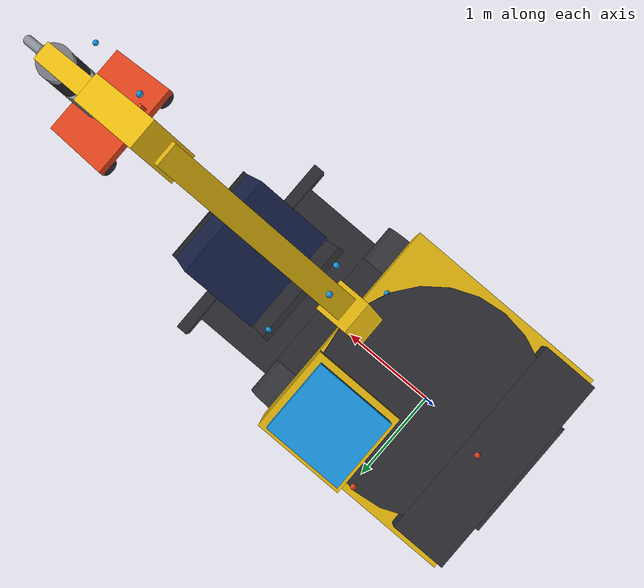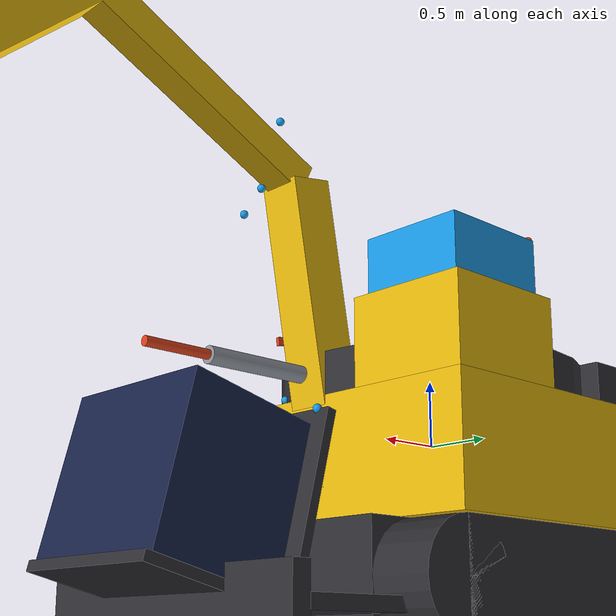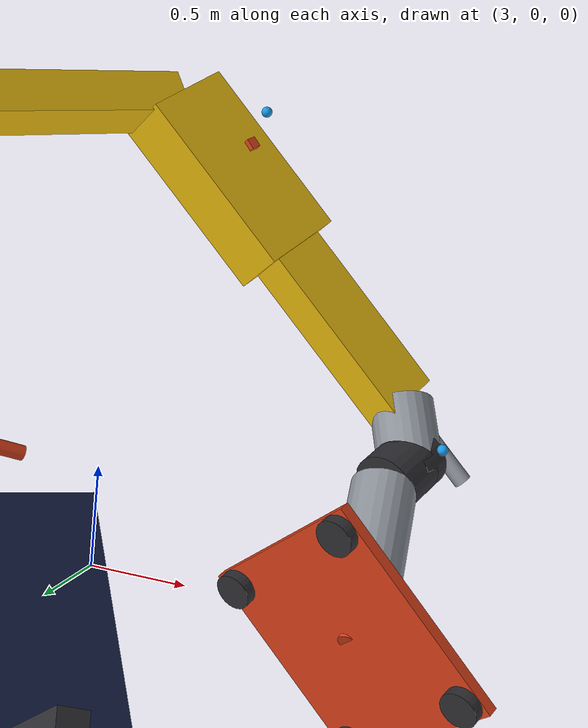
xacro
<?xml version="1.0"?>
<robot name="ecr88" xmlns:xacro="http://www.ros.org/wiki/xacro">

  <!-- ============================ ARGS ============================ -->
  <xacro:arg name="use_meshes"          default="false"/>
  <xacro:arg name="use_ros2_control"    default="false"/>
  <xacro:arg name="model_bucket_fourbar" default="true"/>
  <xacro:arg name="model_cylinders"     default="true"/>
  <xacro:arg name="model_arm_cylinder"  default="false"/>
  <!-- Front fork carriage and the stack of modules riding on it. This is how the
       machine actually feeds itself, so it is on by default. -->
  <xacro:arg name="model_fork"          default="true"/>
  <!-- The module stack on the fork. Off for CalibForkRefPose (step 28), which is recorded with
       the tool held against the BARE backrest, where the stack would otherwise be. -->
  <xacro:arg name="model_panel_stack"   default="true"/>
  <!-- Candidate camera/lidar mount frames. Zero mass, no geometry beyond a marker. -->
  <xacro:arg name="model_sensor_mounts" default="true"/>
  <!-- The five CAN1 IMU frames. On by default: they carry calibrated data, they are
       massless markers, and the SIL loop needs them. -->
  <xacro:arg name="model_imus"          default="true"/>
  <xacro:arg name="mesh_package"        default="xpanner_sim"/>
  <xacro:arg name="mesh_dir"            default="assets/ecr88/meshes"/>
  <xacro:arg name="mesh_visual_ext"     default="dae"/>
  <xacro:arg name="mesh_collision_ext"  default="stl"/>
  <xacro:arg name="ros2_control_plugin" default="mock_components/GenericSystem"/>

  <xacro:property name="mesh_base" value="package://$(arg mesh_package)/$(arg mesh_dir)"/>

  <!-- ==================== GROUND-TRUTH PARAMETERS ==================== -->
  <xacro:include filename="ecr88_params.xacro"/>
  <!-- mass / CoM / inertia / joint limits. Authoritative for every m_*, com_*, inr_*,
       lim_*, eff_*, vel_* and dyn_* property; provenance in resources/ECR88_estimated_dynamics.md -->
  <xacro:include filename="ecr88_dynamics.xacro"/>

  <xacro:property name="half"    value="0.5"/>
  <xacro:property name="half_pi" value="${pi * 0.5}"/>

  <xacro:macro name="inertial_box" params="mass x y z xyz:='0 0 0' rpy:='0 0 0'">
    <inertial>
      <origin xyz="${xyz}" rpy="${rpy}"/>
      <mass value="${mass}"/>
      <inertia ixx="${mass * (y*y + z*z) / 12.0}" ixy="0" ixz="0"
               iyy="${mass * (x*x + z*z) / 12.0}" iyz="0"
               izz="${mass * (x*x + y*y) / 12.0}"/>
    </inertial>
  </xacro:macro>

  <xacro:macro name="inertial_cylinder" params="mass radius length xyz:='0 0 0' rpy:='0 0 0'">
    <inertial>
      <origin xyz="${xyz}" rpy="${rpy}"/>
      <mass value="${mass}"/>
      <inertia ixx="${mass * (3.0*radius*radius + length*length) / 12.0}" ixy="0" ixz="0"
               iyy="${mass * (3.0*radius*radius + length*length) / 12.0}" iyz="0"
               izz="${mass * radius * radius * 0.5}"/>
    </inertial>
  </xacro:macro>

  <!-- Inertia of a uniform sphere (marker / frame-only links). -->
  <xacro:macro name="inertial_sphere" params="mass radius xyz:='0 0 0'">
    <inertial>
      <origin xyz="${xyz}" rpy="0 0 0"/>
      <mass value="${mass}"/>
      <inertia ixx="${2.0 * mass * radius * radius / 5.0}" ixy="0" ixz="0"
               iyy="${2.0 * mass * radius * radius / 5.0}" iyz="0"
               izz="${2.0 * mass * radius * radius / 5.0}"/>
    </inertial>
  </xacro:macro>

  <xacro:macro name="viscol"
               params="name material:='xpanner_yellow'
                       xyz:='0 0 0' rpy:='0 0 0'
                       mesh_xyz:='0 0 0' mesh_rpy:='0 0 0' *prim">
    <visual>
      <xacro:if value="$(arg use_meshes)">
        <origin xyz="${mesh_xyz}" rpy="${mesh_rpy}"/>
        <geometry>
          <mesh filename="${mesh_base}/${name}.$(arg mesh_visual_ext)" scale="1 1 1"/>
        </geometry>
      </xacro:if>
      <xacro:unless value="$(arg use_meshes)">
        <origin xyz="${xyz}" rpy="${rpy}"/>
        <geometry><xacro:insert_block name="prim"/></geometry>
      </xacro:unless>
      <material name="${material}"/>
    </visual>
    <collision>
      <xacro:if value="$(arg use_meshes)">
        <origin xyz="${mesh_xyz}" rpy="${mesh_rpy}"/>
        <geometry>
          <mesh filename="${mesh_base}/${name}_collision.$(arg mesh_collision_ext)" scale="1 1 1"/>
        </geometry>
      </xacro:if>
      <xacro:unless value="$(arg use_meshes)">
        <origin xyz="${xyz}" rpy="${rpy}"/>
        <geometry><xacro:insert_block name="prim"/></geometry>
      </xacro:unless>
    </collision>
  </xacro:macro>

  <xacro:macro name="detail"
               params="material:='xpanner_yellow' xyz:='0 0 0' rpy:='0 0 0' *prim">
    <xacro:unless value="$(arg use_meshes)">
      <visual>
        <origin xyz="${xyz}" rpy="${rpy}"/>
        <geometry><xacro:insert_block name="prim"/></geometry>
        <material name="${material}"/>
      </visual>
      <collision>
        <origin xyz="${xyz}" rpy="${rpy}"/>
        <geometry><xacro:insert_block name="prim"/></geometry>
      </collision>
    </xacro:unless>
  </xacro:macro>

  <xacro:macro name="detail_visual"
               params="material:='xpanner_yellow' xyz:='0 0 0' rpy:='0 0 0' *prim">
    <xacro:unless value="$(arg use_meshes)">
      <visual>
        <origin xyz="${xyz}" rpy="${rpy}"/>
        <geometry><xacro:insert_block name="prim"/></geometry>
        <material name="${material}"/>
      </visual>
    </xacro:unless>
  </xacro:macro>

  <xacro:macro name="member_cylinder" params="radius dx dy dz">
    <cylinder radius="${radius}" length="${sqrt(dx*dx + dy*dy + dz*dz)}"/>
  </xacro:macro>

  <!-- ============================ MATERIALS ============================ -->
  <!-- Cosmetic only. -->
  <material name="xpanner_yellow"><color rgba="0.90 0.72 0.05 1"/></material>
  <material name="xpanner_dark">  <color rgba="0.18 0.18 0.20 1"/></material>
  <material name="xpanner_steel"> <color rgba="0.55 0.57 0.60 1"/></material>
  <material name="xpanner_accent"><color rgba="0.85 0.25 0.10 1"/></material>
  <material name="xpanner_frame"> <color rgba="0.10 0.60 0.90 1"/></material>
  <material name="xpanner_panel"> <color rgba="0.09 0.13 0.28 1"/></material>

  <link name="base_link">
    <xacro:inertial_box mass="${m_base_frame}"
                        x="${lenBottomX}" y="${lenBottomY - geo_track_w - geo_track_w}"
                        z="${lenUppZ1 - lenBottomZ1}"
                        xyz="0 0 ${(lenBottomZ1 + lenUppZ1) * half}"/>
    <xacro:viscol name="base_link" material="xpanner_dark"
                  xyz="0 0 ${(lenBottomZ1 + lenUppZ1) * half}">
      <box size="${lenBottomX} ${lenBottomY - geo_track_w - geo_track_w} ${lenUppZ1 - lenBottomZ1}"/>
    </xacro:viscol>
  </link>

  <link name="dozer_link">
    <xacro:inertial_box mass="${m_blade}"
                        x="${geo_blade_t}" y="${lenBottomY}" z="${geo_blade_h}"
                        xyz="${geo_blade_arm} 0 0"/>
    <!-- Push arms, drawn from the pivot out to the blade so the joint is visible. -->
    <xacro:viscol name="dozer_link" material="xpanner_dark"
                  xyz="${geo_blade_arm * half} 0 0">
      <box size="${geo_blade_arm} ${lenBottomY - geo_track_w} 0.10"/>
    </xacro:viscol>
    <xacro:detail material="xpanner_dark" xyz="${geo_blade_arm} 0 0">
      <box size="${geo_blade_t} ${lenBottomY} ${geo_blade_h}"/>
    </xacro:detail>
  </link>
  <joint name="dozer_joint" type="revolute">
    <parent link="base_link"/>
    <child  link="dozer_link"/>
    <origin xyz="${blade_pivot_x} 0 ${blade_pivot_z}" rpy="0 0 0"/>
    <!-- +Y, so a POSITIVE angle lifts the blade. Matches the boom convention
         (blade up and boom up are both positive about +Y). -->
    <axis xyz="0 1 0"/>
    <limit lower="${jntDozerLower}" upper="${jntDozerUpper}"
           effort="${eff_dozer}" velocity="${vel_dozer}"/>
    <dynamics damping="${dyn_damping}" friction="${dyn_friction}"/>
  </joint>

  <link name="track_left_link">
    <xacro:inertial_box mass="${m_track}"
                        x="${lenBottomX}" y="${geo_track_w}" z="${lenUppZ1 - lenBottomZ1}"
                        xyz="0 0 ${(lenBottomZ1 + lenUppZ1) * half}"/>
    <xacro:viscol name="track_left_link" material="xpanner_dark"
                  xyz="0 0 ${(lenBottomZ1 + lenUppZ1) * half}">
      <box size="${lenBottomX - geo_track_r - geo_track_r} ${geo_track_w} ${geo_track_h}"/>
    </xacro:viscol>
    <xacro:detail material="xpanner_dark"
                  xyz="${geo_track_wheel_dx} 0 ${(lenBottomZ1 + lenUppZ1) * half}"
                  rpy="${half_pi} 0 0">
      <cylinder radius="${geo_track_r}" length="${geo_track_w}"/>
    </xacro:detail>
    <xacro:detail material="xpanner_dark"
                  xyz="${-geo_track_wheel_dx} 0 ${(lenBottomZ1 + lenUppZ1) * half}"
                  rpy="${half_pi} 0 0">
      <cylinder radius="${geo_track_r}" length="${geo_track_w}"/>
    </xacro:detail>
  </link>
  <joint name="track_left_joint" type="fixed">
    <parent link="base_link"/>
    <child  link="track_left_link"/>
    <origin xyz="0 ${(lenBottomY - geo_track_w) * half} 0" rpy="0 0 0"/>
  </joint>

  <link name="track_right_link">
    <xacro:inertial_box mass="${m_track}"
                        x="${lenBottomX}" y="${geo_track_w}" z="${lenUppZ1 - lenBottomZ1}"
                        xyz="0 0 ${(lenBottomZ1 + lenUppZ1) * half}"/>
    <!-- SHAPE: mirror of track_left_link. See the note there. -->
    <xacro:viscol name="track_right_link" material="xpanner_dark"
                  xyz="0 0 ${(lenBottomZ1 + lenUppZ1) * half}">
      <box size="${lenBottomX - geo_track_r - geo_track_r} ${geo_track_w} ${geo_track_h}"/>
    </xacro:viscol>
    <xacro:detail material="xpanner_dark"
                  xyz="${geo_track_wheel_dx} 0 ${(lenBottomZ1 + lenUppZ1) * half}"
                  rpy="${half_pi} 0 0">
      <cylinder radius="${geo_track_r}" length="${geo_track_w}"/>
    </xacro:detail>
    <xacro:detail material="xpanner_dark"
                  xyz="${-geo_track_wheel_dx} 0 ${(lenBottomZ1 + lenUppZ1) * half}"
                  rpy="${half_pi} 0 0">
      <cylinder radius="${geo_track_r}" length="${geo_track_w}"/>
    </xacro:detail>
  </link>
  <joint name="track_right_joint" type="fixed">
    <parent link="base_link"/>
    <child  link="track_right_link"/>
    <origin xyz="0 ${-(lenBottomY - geo_track_w) * half} 0" rpy="0 0 0"/>
  </joint>

  <link name="house_link">
    <xacro:inertial_box mass="${m_house}"
                        x="${lenUppX}" y="${lenUppY}" z="${geo_house_h}"
                        xyz="0 0 ${lenUppZ1 + geo_house_h * half}"/>
    <xacro:viscol name="house_link" material="xpanner_yellow"
                  xyz="0 0 ${lenUppZ1 + geo_deck_h * half}">
      <box size="${lenUppX} ${lenUppY} ${geo_deck_h}"/>
    </xacro:viscol>
    <xacro:detail material="xpanner_dark"
                  xyz="${-(lenUppX * half) + geo_cw_x * half} 0 ${lenUppZ1 + geo_cw_h * half}">
      <box size="${geo_cw_x} ${lenUppY * 0.94} ${geo_cw_h}"/>
    </xacro:detail>
    <xacro:detail material="xpanner_dark"
                  xyz="0 0 ${lenUppZ1 + geo_cw_h * half}">
      <cylinder radius="${lenUppX * half}" length="${geo_cw_h}"/>
    </xacro:detail>
    <xacro:detail material="xpanner_yellow"
                  xyz="${(lenUppX * half) - geo_cab_x * half} ${(lenUppY * half) - geo_cab_y * half} ${lenUppZ1 + geo_deck_h + geo_cab_h * 0.30}">
      <box size="${geo_cab_x} ${geo_cab_y} ${geo_cab_h * 0.60}"/>
    </xacro:detail>
    <xacro:detail material="xpanner_frame"
                  xyz="${(lenUppX * half) - geo_cab_x * half} ${(lenUppY * half) - geo_cab_y * half} ${lenUppZ1 + geo_deck_h + geo_cab_h * 0.80}">
      <box size="${geo_cab_x - geo_cab_upper_inset} ${geo_cab_y - geo_cab_upper_inset} ${geo_cab_h * 0.40}"/>
    </xacro:detail>
  </link>
  <joint name="swing_joint" type="revolute">
    <parent link="base_link"/>
    <child  link="house_link"/>
    <origin xyz="0 0 0" rpy="0 0 0"/>
    <axis xyz="0 0 1"/>
    <!-- ESTIMATE limits (T2). Real machine slews endlessly (T16). -->
    <limit lower="${lim_swing_lower}" upper="${lim_swing_upper}"
           effort="${eff_swing}" velocity="${vel_swing}"/>
    <dynamics damping="${dyn_damping}" friction="${dyn_friction}"/>
  </joint>

  <link name="gnss_main_link">
    <xacro:inertial_sphere mass="${m_marker}" radius="${geo_marker_r}"/>
    <xacro:viscol name="gnss_main_link" material="xpanner_accent">
      <sphere radius="${geo_marker_r}"/>
    </xacro:viscol>
  </link>
  <joint name="gnss_main_joint" type="fixed">
    <parent link="house_link"/>
    <child  link="gnss_main_link"/>
    <origin xyz="${-distAntMainToChs_x} ${-distAntMainToChs_y} ${-distAntMainToChs_z}"
            rpy="0 0 0"/>
  </joint>

  <link name="gnss_aux_link">
    <xacro:inertial_sphere mass="${m_marker}" radius="${geo_marker_r}"/>
    <xacro:viscol name="gnss_aux_link" material="xpanner_accent">
      <sphere radius="${geo_marker_r}"/>
    </xacro:viscol>
  </link>
  <joint name="gnss_aux_joint" type="fixed">
    <parent link="gnss_main_link"/>
    <child  link="gnss_aux_link"/>
    <origin xyz="${distAntMainToAntAux_x} ${distAntMainToAntAux_y} ${distAntMainToAntAux_z}"
            rpy="0 0 0"/>
  </joint>

  <link name="boom_mount_link">
    <xacro:inertial_sphere mass="${m_marker}" radius="${geo_marker_r}"/>
    <xacro:viscol name="boom_mount_link" material="xpanner_steel">
      <sphere radius="${geo_marker_r}"/>
    </xacro:viscol>
  </link>
  <joint name="boom_swing_joint" type="revolute">
    <parent link="house_link"/>
    <child  link="boom_mount_link"/>
    <origin xyz="${distChsToBmMnt_x} ${distChsToBmMnt_y} ${distChsToBmMnt_z}" rpy="0 0 0"/>
    <axis xyz="0 0 1"/>
    <limit lower="${lim_bm_swing_lower}" upper="${lim_bm_swing_upper}"
           effort="${eff_bm_swing}" velocity="${vel_bm_swing}"/>
    <dynamics damping="${dyn_damping}" friction="${dyn_friction}"/>
  </joint>

  <link name="cyl_lrg_bm1_link">
    <xacro:inertial_sphere mass="${m_marker}" radius="${geo_marker_r}"/>
    <xacro:viscol name="cyl_lrg_bm1_link" material="xpanner_frame">
      <sphere radius="${geo_marker_r}"/>
    </xacro:viscol>
  </link>
  <joint name="cyl_lrg_bm1_joint" type="fixed">
    <parent link="boom_mount_link"/>
    <child  link="cyl_lrg_bm1_link"/>
    <origin xyz="${distCylLrgBm1_x} ${distCylLrgBm1_y} ${distCylLrgBm1_z}" rpy="0 0 0"/>
  </joint>

  <link name="boom_link">
    <xacro:inertial_cylinder mass="${m_boom}" radius="${geo_boom_r}"
                             length="${lenBm1 + lenBm2}"
                             xyz="${(lenBm1 + lenBm2) * half} 0 0" rpy="0 ${half_pi} 0"/>
    <xacro:property name="bm_apex_x" value="${(lenBm1 + lenBm2) * geo_boom_apex_frac}"/>
    <xacro:property name="bm_tip_dx" value="${(lenBm1 + lenBm2) - bm_apex_x}"/>
    <!-- foot -> apex -->
    <xacro:viscol name="boom_link" material="xpanner_yellow"
                  xyz="${bm_apex_x * half} 0 ${geo_boom_rise * half}"
                  rpy="0 ${-atan2(geo_boom_rise, bm_apex_x)} 0">
      <box size="${sqrt(bm_apex_x * bm_apex_x + geo_boom_rise * geo_boom_rise)} ${geo_boom_sec_w} ${geo_boom_sec_h}"/>
    </xacro:viscol>
    <!-- apex -> arm pin -->
    <xacro:detail material="xpanner_yellow"
                  xyz="${bm_apex_x + bm_tip_dx * half} 0 ${geo_boom_rise * half}"
                  rpy="0 ${atan2(geo_boom_rise, bm_tip_dx)} 0">
      <box size="${sqrt(bm_tip_dx * bm_tip_dx + geo_boom_rise * geo_boom_rise)} ${geo_boom_sec_w * geo_boom_taper} ${geo_boom_sec_h * geo_boom_taper}"/>
    </xacro:detail>
  </link>
  <joint name="boom_joint" type="revolute">
    <parent link="boom_mount_link"/>
    <child  link="boom_link"/>
    <!-- distBmMntToBm1 is (0,0,0) unless the BoomSwing sensor option is mounted. -->
    <origin xyz="${distBmMntToBm1_x} ${distBmMntToBm1_y} ${distBmMntToBm1_z}" rpy="0 0 0"/>
    <axis xyz="0 1 0"/>
    <limit lower="${lim_boom_lower}" upper="${lim_boom_upper}"
           effort="${eff_boom}" velocity="${vel_boom}"/>
    <dynamics damping="${dyn_damping}" friction="${dyn_friction}"/>
  </joint>

  <link name="cyl_sml_bm1_link">
    <xacro:inertial_sphere mass="${m_marker}" radius="${geo_marker_r}"/>
    <xacro:viscol name="cyl_sml_bm1_link" material="xpanner_frame">
      <sphere radius="${geo_marker_r}"/>
    </xacro:viscol>
  </link>
  <joint name="cyl_sml_bm1_joint" type="fixed">
    <parent link="boom_link"/>
    <child  link="cyl_sml_bm1_link"/>
    <origin xyz="${distCylSmlBm1_x} ${distCylSmlBm1_y} ${distCylSmlBm1_z}" rpy="0 0 0"/>
  </joint>

  <link name="cyl_lrg_arm_link">
    <xacro:inertial_sphere mass="${m_marker}" radius="${geo_marker_r}"/>
    <xacro:viscol name="cyl_lrg_arm_link" material="xpanner_frame">
      <sphere radius="${geo_marker_r}"/>
    </xacro:viscol>
  </link>
  <joint name="cyl_lrg_arm_joint" type="fixed">
    <parent link="boom_link"/>
    <child  link="cyl_lrg_arm_link"/>
    <origin xyz="${lenBm1 + lenBm2 + distCylLrgArm_x} ${distCylLrgArm_y} ${distCylLrgArm_z}"
            rpy="0 0 0"/>
  </joint>

  <!-- =====================================================================
       6. ARM  (stick)
       ===================================================================== -->
  <link name="arm_link">
    <xacro:inertial_cylinder mass="${m_arm}" radius="${geo_arm_r}" length="${lenArm}"
                             xyz="${lenArm * half} 0 0" rpy="0 ${half_pi} 0"/>
    <xacro:viscol name="arm_link" material="xpanner_yellow"
                  xyz="${lenArm * 0.25} 0 0">
      <box size="${lenArm * half} ${geo_arm_sec_w} ${geo_arm_sec_h}"/>
    </xacro:viscol>
    <!-- Tapered tip half. Every dipper narrows toward the bucket pin. Cosmetic. -->
    <xacro:detail material="xpanner_yellow"
                  xyz="${lenArm * 0.75} 0 0">
      <box size="${lenArm * half} ${geo_arm_sec_w * geo_arm_taper} ${geo_arm_sec_h * geo_arm_taper}"/>
    </xacro:detail>
  </link>
  <joint name="arm_joint" type="revolute">
    <parent link="boom_link"/>
    <child  link="arm_link"/>
    <origin xyz="${lenBm1 + lenBm2} 0 0" rpy="0 0 0"/>
    <axis xyz="0 1 0"/>
    <limit lower="${lim_arm_lower}" upper="${lim_arm_upper}"
           effort="${eff_arm}" velocity="${vel_arm}"/>
    <dynamics damping="${dyn_damping}" friction="${dyn_friction}"/>
  </joint>

  <xacro:macro name="hyd_cylinder"
               params="name parent driver anchor_xyz phi_mult phi_off d_mult d_off
                       len_min bore rod d_lo d_hi m_barrel m_rod">
    <link name="${name}_barrel">
      <xacro:inertial_cylinder mass="${m_barrel}" radius="${bore * half + cyl_wall}"
                               length="${len_min * cyl_barrel_frac}"
                               xyz="${len_min * cyl_barrel_frac * half} 0 0" rpy="0 ${half_pi} 0"/>
      <xacro:detail_visual material="xpanner_steel"
                    xyz="${len_min * cyl_barrel_frac * half} 0 0" rpy="0 ${half_pi} 0">
        <cylinder radius="${bore * half + cyl_wall}" length="${len_min * cyl_barrel_frac}"/>
      </xacro:detail_visual>
    </link>
    <joint name="${name}_pitch" type="revolute">
      <parent link="${parent}"/>
      <child  link="${name}_barrel"/>
      <origin xyz="${anchor_xyz}" rpy="0 0 0"/>
      <axis xyz="0 1 0"/>
      <mimic joint="${driver}" multiplier="${phi_mult}" offset="${phi_off}"/>
      <limit lower="${-pi}" upper="${pi}"
             effort="${cyl_relief_pa * pi / 4 * bore * bore * 0.1}" velocity="2.0"/>
    </joint>

    <link name="${name}_rod">
      <xacro:inertial_cylinder mass="${m_rod}" radius="${rod * half}" length="${len_min}"
                               xyz="${len_min * half} 0 0" rpy="0 ${half_pi} 0"/>
      <xacro:detail_visual material="xpanner_accent"
                    xyz="${len_min * half} 0 0" rpy="0 ${half_pi} 0">
        <cylinder radius="${rod * half}" length="${len_min}"/>
      </xacro:detail_visual>
    </link>
    <joint name="${name}_extend" type="prismatic">
      <parent link="${name}_barrel"/>
      <child  link="${name}_rod"/>
      <origin xyz="0 0 0" rpy="0 0 0"/>
      <axis xyz="1 0 0"/>
      <mimic joint="${driver}" multiplier="${d_mult}" offset="${d_off}"/>
      <limit lower="${d_lo}" upper="${d_hi}"
             effort="${cyl_relief_pa * pi / 4 * bore * bore}" velocity="0.30"/>
    </joint>
  </xacro:macro>

  <xacro:if value="$(arg model_cylinders)">
    <xacro:hyd_cylinder name="cyl_boom" parent="boom_mount_link" driver="boom_joint"
                        anchor_xyz="${distCylLrgBm1_x} ${distCylLrgBm1_y} ${distCylLrgBm1_z}"
                        phi_mult="${cyl_boom_phi_mult}" phi_off="${cyl_boom_phi_off}"
                        d_mult="${cyl_boom_d_mult}"     d_off="${cyl_boom_d_off}"
                        len_min="${cyl_boom_len_min}" bore="${cyl_boom_bore}" rod="${cyl_boom_rod}"
                        d_lo="-0.05" d_hi="0.15"
                        m_barrel="${m_cyl_boom_barrel}" m_rod="${m_cyl_boom_rod}"/>
    <xacro:if value="$(arg model_arm_cylinder)">
    <xacro:hyd_cylinder name="cyl_arm" parent="boom_link" driver="arm_joint"
                        anchor_xyz="${lenBm1 + lenBm2 + distCylLrgArm_x} ${distCylLrgArm_y} ${distCylLrgArm_z}"
                        phi_mult="${cyl_arm_phi_mult}" phi_off="${cyl_arm_phi_off}"
                        d_mult="${cyl_arm_d_mult}"     d_off="${cyl_arm_d_off}"
                        len_min="${cyl_arm_len_min}" bore="${cyl_arm_bore}" rod="${cyl_arm_rod}"
                        d_lo="0.0" d_hi="0.90"
                        m_barrel="${m_cyl_arm_barrel}" m_rod="${m_cyl_arm_rod}"/>
    </xacro:if>
  </xacro:if>

  <link name="ground_link">
    <xacro:inertial_cylinder mass="${m_gnd_link}" radius="${geo_linkage_r}"
                             length="${lenGndLink}"
                             xyz="${(distArmToInpLink_x - lenArm) * half} ${distArmToInpLink_y * half} ${distArmToInpLink_z * half}"
                             rpy="0 ${atan2(distArmToInpLink_x - lenArm, distArmToInpLink_z)} 0"/>
    <xacro:viscol name="ground_link" material="xpanner_steel"
                  xyz="${(distArmToInpLink_x - lenArm) * half} ${distArmToInpLink_y * half} ${distArmToInpLink_z * half}"
                  rpy="0 ${atan2(distArmToInpLink_x - lenArm, distArmToInpLink_z)} 0">
      <xacro:member_cylinder radius="${geo_linkage_r}"
                             dx="${distArmToInpLink_x - lenArm}"
                             dy="${distArmToInpLink_y}"
                             dz="${distArmToInpLink_z}"/>
    </xacro:viscol>
  </link>
  <joint name="ground_link_joint" type="fixed">
    <parent link="arm_link"/>
    <child  link="ground_link"/>
    <!-- origin = arm tip = bucket pin. The ground link's own direction is derived by
         atan2 above rather than taken from angArmToGndLink - see T14c. -->
    <origin xyz="${lenArm} 0 0" rpy="0 0 0"/>
  </joint>

  <link name="output_link">
    <xacro:inertial_cylinder mass="${m_outp_link}" radius="${geo_linkage_r}"
                             length="${lenOutpLink}"
                             xyz="${lenOutpLink * half} 0 0" rpy="0 ${half_pi} 0"/>
    <xacro:viscol name="output_link" material="xpanner_steel"
                  xyz="${lenOutpLink * half} 0 0" rpy="0 ${half_pi} 0">
      <cylinder radius="${geo_linkage_r}" length="${lenOutpLink}"/>
    </xacro:viscol>
  </link>
  <joint name="bucket_joint" type="revolute">
    <parent link="ground_link"/>
    <child  link="output_link"/>
    <origin xyz="0 0 0" rpy="0 0 0"/>
    <axis xyz="0 1 0"/>
    <limit lower="${lim_bucket_lower}" upper="${lim_bucket_upper}"
           effort="${eff_bucket}" velocity="${vel_bucket}"/>
    <dynamics damping="${dyn_damping}" friction="${dyn_friction}"/>
  </joint>

  <xacro:if value="$(arg model_bucket_fourbar)">
    <!-- INPUT LINK (power/crank link), pinned to the arm at distArmToInpLink. -->
    <link name="input_link">
      <xacro:inertial_cylinder mass="${m_inp_link}" radius="${geo_linkage_r}"
                               length="${lenInpLink}"
                               xyz="${lenInpLink * half} 0 0" rpy="0 ${half_pi} 0"/>
      <xacro:viscol name="input_link" material="xpanner_steel"
                    xyz="${lenInpLink * half} 0 0" rpy="0 ${half_pi} 0">
        <cylinder radius="${geo_linkage_r}" length="${lenInpLink}"/>
      </xacro:viscol>
    </link>
    <joint name="input_link_joint" type="revolute">
      <parent link="ground_link"/>
      <child  link="input_link"/>
      <!-- ground_link origin is the bucket pin, so the input pin is offset by the
           ground-link vector: distArmToInpLink - (lenArm, 0, 0). -->
      <origin xyz="${distArmToInpLink_x - lenArm} ${distArmToInpLink_y} ${distArmToInpLink_z}"
              rpy="0 0 0"/>
      <axis xyz="0 1 0"/>
      <limit lower="${lim_inp_link_lower}" upper="${lim_inp_link_upper}"
             effort="${eff_inp_link}" velocity="${vel_inp_link}"/>
      <dynamics damping="${dyn_damping}" friction="${dyn_friction}"/>
      <!-- PLACEHOLDER COUPLING - see the MIMIC / closed-loop block above. -->
      <mimic joint="bucket_joint" multiplier="${bkt_mimic_mult}" offset="${bkt_mimic_off}"/>
    </joint>

    <!-- CONNECTING ROD (idler). This is the CUT member: its far end
         (+lenConnRod along X) must coincide with output_link + lenOutpLink along X. -->
    <link name="conn_rod_link">
      <xacro:inertial_cylinder mass="${m_conn_rod}" radius="${geo_linkage_r}"
                               length="${lenConnRod}"
                               xyz="${lenConnRod * half} 0 0" rpy="0 ${half_pi} 0"/>
      <xacro:viscol name="conn_rod_link" material="xpanner_steel"
                    xyz="${lenConnRod * half} 0 0" rpy="0 ${half_pi} 0">
        <cylinder radius="${geo_linkage_r}" length="${lenConnRod}"/>
      </xacro:viscol>
    </link>
    <joint name="conn_rod_joint" type="revolute">
      <parent link="input_link"/>
      <child  link="conn_rod_link"/>
      <origin xyz="${lenInpLink} 0 0" rpy="0 0 0"/>
      <axis xyz="0 1 0"/>
      <!-- Cannot be mimicked: no legal URDF expression closes the loop. Free joint. -->
      <limit lower="${lim_conn_rod_lower}" upper="${lim_conn_rod_upper}"
             effort="${eff_conn_rod}" velocity="${vel_conn_rod}"/>
      <dynamics damping="${dyn_damping}" friction="${dyn_friction}"/>
    </joint>
  </xacro:if>

  <link name="tilt_mount_link">
    <xacro:inertial_cylinder mass="${m_tilt_mount}" radius="${geo_tr_r}"
                             length="${sqrt(distTiltMntToTilt_x*distTiltMntToTilt_x + distTiltMntToTilt_y*distTiltMntToTilt_y + distTiltMntToTilt_z*distTiltMntToTilt_z)}"
                             xyz="${distTiltMntToTilt_x * half} ${distTiltMntToTilt_y * half} ${distTiltMntToTilt_z * half}"
                             rpy="0 ${atan2(distTiltMntToTilt_x, distTiltMntToTilt_z)} 0"/>
    <xacro:viscol name="tilt_mount_link" material="xpanner_steel"
                  xyz="${distTiltMntToTilt_x * half} ${distTiltMntToTilt_y * half} ${distTiltMntToTilt_z * half}"
                  rpy="0 ${atan2(distTiltMntToTilt_x, distTiltMntToTilt_z)} 0">
      <xacro:member_cylinder radius="${geo_tr_r}"
                             dx="${distTiltMntToTilt_x}"
                             dy="${distTiltMntToTilt_y}"
                             dz="${distTiltMntToTilt_z}"/>
    </xacro:viscol>
  </link>
  <joint name="tilt_mount_joint" type="fixed">
    <parent link="output_link"/>
    <child  link="tilt_mount_link"/>
    <origin xyz="${distOutpLinkToTiltMnt_x} ${distOutpLinkToTiltMnt_y} ${distOutpLinkToTiltMnt_z}"
            rpy="0 ${angOutpLinkToTiltMnt + angTiltMntToTilt} 0"/>
  </joint>

  <!-- TILT. Axis ASSUMED +X (T3): a tiltrotator tilts the tool sideways, i.e. rolls
       about the fore-aft axis, perpendicular to the rotator's Z. Not in any source. -->
  <link name="tilt_link">
    <xacro:inertial_cylinder mass="${m_tilt}" radius="${geo_tr_r}" length="${geo_tr_r}"/>
    <xacro:viscol name="tilt_link" material="xpanner_dark">
      <cylinder radius="${geo_tr_r}" length="${geo_tr_r}"/>
    </xacro:viscol>
  </link>
  <joint name="tilt_joint" type="revolute">
    <parent link="tilt_mount_link"/>
    <child  link="tilt_link"/>
    <origin xyz="${distTiltMntToTilt_x} ${distTiltMntToTilt_y} ${distTiltMntToTilt_z}"
            rpy="0 0 0"/>
    <axis xyz="1 0 0"/>
    <limit lower="${lim_tilt_lower}" upper="${lim_tilt_upper}"
           effort="${eff_tilt}" velocity="${vel_tilt}"/>
    <dynamics damping="${dyn_damping}" friction="${dyn_friction}"/>
  </joint>

  <!-- ROTATOR. Continuous about Z - endless tool rotation. The rotator body is drawn
       spanning Rot -> Att, whose length is DERIVED from distRotToAtt. -->
  <link name="rotator_link">
    <xacro:inertial_cylinder mass="${m_rotator}" radius="${geo_tr_r}"
                             length="${sqrt(distRotToAtt_x*distRotToAtt_x + distRotToAtt_y*distRotToAtt_y + distRotToAtt_z*distRotToAtt_z)}"
                             xyz="${distRotToAtt_x * half} ${distRotToAtt_y * half} ${distRotToAtt_z * half}"/>
    <xacro:viscol name="rotator_link" material="xpanner_dark"
                  xyz="${distRotToAtt_x * half} ${distRotToAtt_y * half} ${distRotToAtt_z * half}">
      <xacro:member_cylinder radius="${geo_tr_r}"
                             dx="${distRotToAtt_x}" dy="${distRotToAtt_y}" dz="${distRotToAtt_z}"/>
    </xacro:viscol>
  </link>
  <joint name="rotator_joint" type="continuous">
    <parent link="tilt_link"/>
    <child  link="rotator_link"/>
    <!-- "Tilt = Rot": tilt and rotate share a point -> zero translation. -->
    <origin xyz="0 0 0" rpy="0 0 0"/>
    <axis xyz="0 0 1"/>
    <limit effort="${eff_rotator}" velocity="${vel_rotator}"/>
    <dynamics damping="${dyn_damping}" friction="${dyn_friction}"/>
  </joint>

  <link name="attachment_link">
    <xacro:inertial_cylinder mass="${m_attachment}" radius="${geo_tr_r}"
                             length="${sqrt(distAttToProbe_x*distAttToProbe_x + distAttToProbe_y*distAttToProbe_y + distAttToProbe_z*distAttToProbe_z)}"
                             xyz="${distAttToProbe_x * half} ${distAttToProbe_y * half} ${distAttToProbe_z * half}"
                             rpy="0 ${atan2(distAttToProbe_x, distAttToProbe_z)} 0"/>
    <xacro:viscol name="attachment_link" material="xpanner_steel"
                  xyz="${distAttToProbe_x * half} ${distAttToProbe_y * half} ${distAttToProbe_z * half}"
                  rpy="0 ${atan2(distAttToProbe_x, distAttToProbe_z)} 0">
      <xacro:member_cylinder radius="${geo_tr_r}"
                             dx="${distAttToProbe_x}" dy="${distAttToProbe_y}" dz="${distAttToProbe_z}"/>
    </xacro:viscol>
  </link>
  <joint name="attachment_joint" type="fixed">
    <parent link="rotator_link"/>
    <child  link="attachment_link"/>
    <origin xyz="${distRotToAtt_x} ${distRotToAtt_y} ${distRotToAtt_z}"
            rpy="0 ${angRotToAtt} 0"/>
  </joint>

  <link name="probe_link">
    <xacro:inertial_cylinder mass="${m_probe}" radius="${geo_linkage_r}"
                             length="${sqrt(distProbeToContactSurface_x*distProbeToContactSurface_x + distProbeToContactSurface_y*distProbeToContactSurface_y + distProbeToContactSurface_z*distProbeToContactSurface_z)}"
                             xyz="${distProbeToContactSurface_x * half} ${distProbeToContactSurface_y * half} ${distProbeToContactSurface_z * half}"
                             rpy="0 ${atan2(distProbeToContactSurface_x, distProbeToContactSurface_z)} 0"/>
    <xacro:viscol name="probe_link" material="xpanner_accent"
                  xyz="${distProbeToContactSurface_x * half} ${distProbeToContactSurface_y * half} ${distProbeToContactSurface_z * half}"
                  rpy="0 ${atan2(distProbeToContactSurface_x, distProbeToContactSurface_z)} 0">
      <xacro:member_cylinder radius="${geo_linkage_r}"
                             dx="${distProbeToContactSurface_x}"
                             dy="${distProbeToContactSurface_y}"
                             dz="${distProbeToContactSurface_z}"/>
    </xacro:viscol>
  </link>
  <joint name="probe_joint" type="fixed">
    <parent link="attachment_link"/>
    <child  link="probe_link"/>
    <origin xyz="${distAttToProbe_x} ${distAttToProbe_y} ${distAttToProbe_z}"
            rpy="0 ${angAttToProbe} 0"/>
  </joint>

  <link name="contact_surface_link">
    <xacro:inertial_box mass="${m_contact_surface}"
                        x="${geo_pad_x}" y="${geo_pad_y}" z="${geo_pad_t}"
                        xyz="0 0 ${geo_pad_t * half}"/>
    <xacro:viscol name="contact_surface_link" material="xpanner_accent"
                  xyz="0 0 ${geo_pad_t * half}">
      <box size="${geo_pad_x} ${geo_pad_y} ${geo_pad_t}"/>
    </xacro:viscol>
    <xacro:property name="cup_dx" value="${geo_pad_x * half - geo_suction_cup_r}"/>
    <xacro:property name="cup_dy" value="${geo_pad_y * half - geo_suction_cup_r}"/>
    <xacro:detail_visual material="xpanner_dark" xyz="${ cup_dx} ${ cup_dy} ${-geo_suction_cup_h * half}">
      <cylinder radius="${geo_suction_cup_r}" length="${geo_suction_cup_h}"/>
    </xacro:detail_visual>
    <xacro:detail_visual material="xpanner_dark" xyz="${ cup_dx} ${-cup_dy} ${-geo_suction_cup_h * half}">
      <cylinder radius="${geo_suction_cup_r}" length="${geo_suction_cup_h}"/>
    </xacro:detail_visual>
    <xacro:detail_visual material="xpanner_dark" xyz="${-cup_dx} ${ cup_dy} ${-geo_suction_cup_h * half}">
      <cylinder radius="${geo_suction_cup_r}" length="${geo_suction_cup_h}"/>
    </xacro:detail_visual>
    <xacro:detail_visual material="xpanner_dark" xyz="${-cup_dx} ${-cup_dy} ${-geo_suction_cup_h * half}">
      <cylinder radius="${geo_suction_cup_r}" length="${geo_suction_cup_h}"/>
    </xacro:detail_visual>
  </link>
  <joint name="contact_surface_joint" type="fixed">
    <parent link="probe_link"/>
    <child  link="contact_surface_link"/>
    <origin xyz="${distProbeToContactSurface_x} ${distProbeToContactSurface_y} ${distProbeToContactSurface_z}"
            rpy="0 ${angProbeToContactSurface} 0"/>
  </joint>

  <xacro:if value="$(arg model_fork)">
    <xacro:property name="stack_depth" value="${panels_per_stack * geo_panel_t}"/>

    <!-- forkBack: firmware frame, zero mass. -->
    <link name="fork_back_link">
      <xacro:inertial_sphere mass="${m_marker}" radius="${geo_marker_r}"/>
      <xacro:detail_visual material="xpanner_accent"><sphere radius="${geo_marker_r}"/></xacro:detail_visual>
    </link>
    <joint name="fork_back_joint" type="fixed">
      <parent link="base_link"/>
      <child  link="fork_back_link"/>
      <origin xyz="${distUcToForkBackX} ${distUcToForkBackY} ${distUcToForkBackZ}"
              rpy="0 ${angForkUpLimit} 0"/>
    </joint>

    <!-- Carriage: pallet base along forkBack +X, backrest along +Z, square to each other.
         Its origin is the base/backrest corner, stack_bottom below cup height. -->
    <link name="fork_link">
      <xacro:inertial_box mass="${m_fork}"
                          x="${geo_fork_len}" y="${LenPLWidth}" z="${geo_fork_t}"
                          xyz="${geo_fork_len * half} 0 ${-geo_fork_t * half}"/>
      <xacro:viscol name="fork_link" material="xpanner_dark"
                    xyz="${geo_fork_len * half} 0 ${-geo_fork_t * half}">
        <box size="${geo_fork_len} ${LenPLWidth} ${geo_fork_t}"/>
      </xacro:viscol>
      <xacro:detail material="xpanner_dark"
                    xyz="${-geo_fork_t * half} 0 ${geo_fork_back_h * half}">
        <box size="${geo_fork_t} ${LenPLWidth} ${geo_fork_back_h}"/>
      </xacro:detail>
    </link>
    <joint name="fork_joint" type="fixed">
      <parent link="fork_back_link"/>
      <child  link="fork_link"/>
      <origin xyz="0 0 ${-LenPanelHeight * half}" rpy="0 0 0"/>
    </joint>

    <xacro:if value="$(arg model_panel_stack)">
    <link name="panel_stack_link">
      <xacro:inertial_box mass="${m_panel * panels_per_stack}"
                          x="${stack_depth}" y="${LenPLWidth}" z="${LenPanelHeight}"
                          xyz="${distForkBackToPanelTopX - stack_depth * half} 0 0"/>
      <xacro:viscol name="panel_stack_link" material="xpanner_panel"
                    xyz="${distForkBackToPanelTopX - stack_depth * half} 0 0">
        <box size="${stack_depth} ${LenPLWidth} ${LenPanelHeight}"/>
      </xacro:viscol>
    </link>
    <joint name="panel_stack_joint" type="fixed">
      <parent link="fork_back_link"/>
      <child  link="panel_stack_link"/>
      <origin xyz="0 0 0" rpy="0 0 0"/>
    </joint>
    </xacro:if>

    <!-- panelTop: the firmware's pick frame. contact_surface must reach this pose. -->
    <link name="panel_top_link">
      <xacro:inertial_sphere mass="${m_marker}" radius="${geo_marker_r}"/>
    </link>
    <joint name="panel_top_joint" type="fixed">
      <parent link="fork_back_link"/>
      <child  link="panel_top_link"/>
      <origin xyz="${distForkBackToPanelTopX} ${distForkBackToPanelTopY} ${distForkBackToPanelTopZ}"
              rpy="0 ${half_pi} 0"/>
    </joint>

    <!-- panelTopWithMargin: where ApproachPanel starts. -->
    <link name="panel_pick_approach_link">
      <xacro:inertial_sphere mass="${m_marker}" radius="${geo_marker_r}"/>
    </link>
    <joint name="panel_pick_approach_joint" type="fixed">
      <parent link="panel_top_link"/>
      <child  link="panel_pick_approach_link"/>
      <origin xyz="0 0 ${TarPanelPickupMargin}" rpy="0 0 0"/>
    </joint>

    <!-- panelLiftPosn: the Placing/Lift target (variant specific). -->
    <link name="panel_lift_posn_link">
      <xacro:inertial_sphere mass="${m_marker}" radius="${geo_marker_r}"/>
    </link>
    <joint name="panel_lift_posn_joint" type="fixed">
      <parent link="panel_top_link"/>
      <child  link="panel_lift_posn_link"/>
      <origin xyz="${distPanelTopToLiftPosnX} 0 ${distPanelTopToLiftPosnZ}" rpy="0 0 0"/>
    </joint>
  </xacro:if>

  <xacro:if value="$(arg model_sensor_mounts)">
    <xacro:macro name="cam_mount" params="name parent xyz rpy">
      <link name="${name}">
        <xacro:inertial_sphere mass="${m_marker}" radius="${geo_marker_r}"/>
        <xacro:detail_visual material="xpanner_frame">
          <sphere radius="${geo_marker_r}"/>
        </xacro:detail_visual>
      </link>
      <joint name="${name}_joint" type="fixed">
        <parent link="${parent}"/>
        <child  link="${name}"/>
        <origin xyz="${xyz}" rpy="${rpy}"/>
      </joint>
    </xacro:macro>

    <!-- Cab roof, front edge, looking forward and down. The operator's own viewpoint. -->
    <xacro:cam_mount name="cam_cab_roof" parent="house_link"
                     xyz="${lenUppX * half - 0.10} ${lenUppY * half - 0.50} ${lenUppZ1 + geo_house_h - 0.05}"
                     rpy="0 ${pi/180*25} 0"/>
    <xacro:cam_mount name="cam_house_front" parent="house_link"
                     xyz="1.00 -0.55 0.30" rpy="0 ${-pi/180*10} ${-pi/180*20}"/>
    <!-- Mid boom, outboard side, aimed along the boom at the tool. -->
    <xacro:cam_mount name="cam_boom_mid" parent="boom_link"
                     xyz="${(lenBm1 + lenBm2) * geo_boom_apex_frac} ${-(geo_boom_sec_w * half + 0.08)} ${geo_boom_rise * 0.6}"
                     rpy="0 ${pi/180*35} 0"/>
    <xacro:cam_mount name="cam_arm_root" parent="arm_link"
                     xyz="0.35 -0.24 0.30" rpy="0 ${pi/180*50} ${pi/180*30}"/>
    <!-- On the tool, above the cups, looking straight down the suction axis. -->
    <xacro:cam_mount name="cam_tool" parent="attachment_link"
                     xyz="0.0 0.0 -0.10" rpy="0 ${half_pi} 0"/>
    <xacro:cam_mount name="cam_tool_side" parent="rotator_link"
                     xyz="0.0 ${-(geo_tr_r + 0.22)} -0.15"
                     rpy="${-pi/180*55} ${pi/180*60} 0"/>
    <!-- On the fork backrest, looking back at the top of the stack. Sees the pick
         point without depending on where the boom happens to be. -->
    <xacro:cam_mount name="cam_fork_mast" parent="fork_link"
                     xyz="0.0 0.50 ${geo_fork_back_h}" rpy="0 ${pi/180*30} ${pi/180*15}"/>
  </xacro:if>

  <xacro:if value="$(arg model_imus)">
    <xacro:macro name="imu_mount" params="name parent xyz rpy">
      <link name="${name}">
        <xacro:inertial_sphere mass="${m_marker}" radius="${geo_marker_r}"/>
        <xacro:detail_visual material="xpanner_accent">
          <box size="${geo_marker_r*2} ${geo_marker_r*2} ${geo_marker_r}"/>
        </xacro:detail_visual>
      </link>
      <joint name="${name}_joint" type="fixed">
        <parent link="${parent}"/>
        <child  link="${name}"/>
        <origin xyz="${xyz}" rpy="${rpy}"/>
      </joint>
    </xacro:macro>

    <!-- imuChs. Flat, yawed 101.012 deg. Position: in the house, low and central. -->
    <xacro:imu_mount name="imu_chs" parent="house_link"
                     xyz="0.20 0.30 ${lenUppZ1 + 0.25}"
                     rpy="${imu_rpy_chs}"/>
    <!-- imuBm1. Side plate at 32.447 deg. Position: outboard face near the boom foot. -->
    <xacro:imu_mount name="imu_boom" parent="boom_link"
                     xyz="0.70 ${-geo_boom_sec_w * half - 0.02} 0.20"
                     rpy="${imu_rpy_boom}"/>
    <!-- imuArm. Side plate at -6.043 deg. -->
    <xacro:imu_mount name="imu_arm" parent="arm_link"
                     xyz="0.45 ${-geo_arm_sec_w * half - 0.02} 0.12"
                     rpy="${imu_rpy_arm}"/>
    <xacro:if value="$(arg model_bucket_fourbar)">
      <xacro:imu_mount name="imu_link" parent="input_link"
                       xyz="${lenInpLink * half} ${-geo_linkage_r - 0.02} 0"
                       rpy="${imu_rpy_link}"/>
    </xacro:if>
    <xacro:imu_mount name="imu_tilt" parent="tilt_link"
                     xyz="0.05 0.0 -0.08"
                     rpy="${imu_rpy_tilt}"/>
  </xacro:if>

  <xacro:macro name="ecr88_ros2_control_joint" params="name">
    <joint name="${name}">
      <command_interface name="position"/>
      <command_interface name="velocity"/>
      <state_interface name="position"/>
      <state_interface name="velocity"/>
      <state_interface name="effort"/>
    </joint>
  </xacro:macro>

  <xacro:if value="$(arg use_ros2_control)">
    <ros2_control name="ecr88_system" type="system">
      <hardware>
        <plugin>$(arg ros2_control_plugin)</plugin>
      </hardware>
      <xacro:ecr88_ros2_control_joint name="swing_joint"/>
      <xacro:ecr88_ros2_control_joint name="boom_joint"/>
      <xacro:ecr88_ros2_control_joint name="arm_joint"/>
      <xacro:ecr88_ros2_control_joint name="bucket_joint"/>
      <xacro:ecr88_ros2_control_joint name="tilt_joint"/>
      <xacro:ecr88_ros2_control_joint name="rotator_joint"/>
      <xacro:ecr88_ros2_control_joint name="boom_swing_joint"/>
      <xacro:ecr88_ros2_control_joint name="dozer_joint"/>
    </ros2_control>
  </xacro:if>

</robot>

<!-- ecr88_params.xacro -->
<robot xmlns:xacro="http://www.ros.org/wiki/xacro" name="ecr88_params">

  <!-- ========================================================================
       [1] BUILD FLAGS
       ======================================================================== -->

  <xacro:property name="use_meshes"            value="false"/>
  <xacro:property name="mesh_dir"              value="package://xpanner_sim/assets/ecr88/meshes"/>
  <xacro:property name="mesh_ext"              value=".obj"/>

  <xacro:property name="collision_from_primitives" value="true"/>

  <!-- Emit the Probe / ContactSurface / Ant* frames as zero-mass fixed links.
       ContactSurface is the TCP we publish to ROS 2. -->
  <xacro:property name="publish_tool_frames"   value="true"/>
  <xacro:property name="tcp_frame"             value="contact_surface"/>

  <xacro:arg name="machine_variant" default="ECR88_US1_2P1M"/>
  <xacro:property name="machine_variant"       value="$(arg machine_variant)"/>

  <xacro:property name="cfg_machine_model"     value="ECR88"/>
  <xacro:property name="cfg_boom"              value="3.5m_standard"/>
  <xacro:property name="cfg_dual_boom_enable"  value="false"/>
  <!-- BoomSwing sensor mounted on BmMnt. distBmMntToBm1 is non-zero ONLY when
       this is true; it is (0,0,0) here. -->
  <xacro:property name="cfg_boomswing_sensor_on_bmmnt" value="false"/>
  <xacro:property name="cfg_tilt_coupler_enable"       value="false"/>
  <xacro:property name="cfg_tilt_rotator_model"        value="JK"/>
  <!-- T8: "On Link" or "On Bkt". The deck gives NO mounting offset for either
       option, so the IMU frame is currently coincident with its parent. -->
  <xacro:property name="cfg_bkt_imu_mount"     value="On Link"/>

  <!-- chassis (house) -> boom mount.
       Y is negative: MC1 measures "Roll Length" +0.159 and X1 PanelLift
       applies *(-1). X (= MC1 "Pitch Length") is NOT negated. -->
  <xacro:property name="distChsToBmMntX"       value="0.94"/>
  <xacro:property name="distChsToBmMntY"       value="-0.15"/>
  <xacro:property name="distChsToBmMntZ"       value="0.0"/>

  <!-- boom mount -> boom1. Exists as a parameter purely to carry the
       BoomSwing sensor option (cfg_boomswing_sensor_on_bmmnt). Zero here. -->
  <xacro:property name="distBmMntToBm1X"       value="0.0"/>
  <xacro:property name="distBmMntToBm1Y"       value="0.0"/>
  <xacro:property name="distBmMntToBm1Z"       value="0.0"/>

  <xacro:property name="distArmToInpLinkY"     value="0.0"/>
  <xacro:property name="distArmToInpLinkZ"     value="0.0185"/>

  <!-- output link -> tilt mount. Coincident frames, kept for chain clarity. -->
  <xacro:property name="distOutpLinkToTiltMntX" value="0.0"/>
  <xacro:property name="distOutpLinkToTiltMntY" value="0.0"/>
  <xacro:property name="distOutpLinkToTiltMntZ" value="0.0"/>

  <xacro:property name="distTiltMntToTiltX"    value="0.28"/>
  <xacro:property name="distTiltMntToTiltY"    value="0.0"/>
  <xacro:property name="distTiltMntToTiltZ"    value="-0.22"/>

  <!-- rotator -> attachment (Att. = Attachment Centre Of Rotation) -->
  <xacro:property name="distRotToAttX"         value="0.0"/>
  <xacro:property name="distRotToAttY"         value="0.0"/>
  <xacro:property name="distRotToAttZ"         value="-0.2615"/>

  <xacro:property name="distAttToProbeY"       value="0.0"/>
  <xacro:property name="distProbeToContactSurfaceY" value="0.0"/>
  <xacro:property name="distAttToContactSurfaceY"   value="0.0"/>

  <xacro:property name="distCylLrgBm1X"        value="0.272"/>
  <xacro:property name="distCylLrgBm1Y"        value="0.0"/>
  <xacro:property name="distCylLrgBm1Z"        value="0.391"/>

  <xacro:property name="distCylSmlBm1X"        value="1.715"/>
  <xacro:property name="distCylSmlBm1Y"        value="0.0"/>
  <xacro:property name="distCylSmlBm1Z"        value="0.58"/>

  <!-- Bm2 option inactive in this build (cfg_dual_boom_enable = false). -->
  <xacro:property name="distCylLrgBm2X"        value="0.0"/>
  <xacro:property name="distCylLrgBm2Y"        value="0.0"/>
  <xacro:property name="distCylLrgBm2Z"        value="0.0"/>

  <xacro:property name="distCylSmlBm2X"        value="0.0"/>
  <xacro:property name="distCylSmlBm2Y"        value="0.0"/>
  <xacro:property name="distCylSmlBm2Z"        value="0.0"/>

  <xacro:property name="distCylLrgArmX"        value="-1.508"/>
  <xacro:property name="distCylLrgArmY"        value="0.0"/>
  <xacro:property name="distCylLrgArmZ"        value="1.08"/>

  <xacro:property name="lenBm1"                value="3.55"/>
  <!-- lenBm2 = 0 => dual-boom segment absent. Emitted as a zero-length fixed
       joint, not deleted, so link indices are variant-stable. -->
  <xacro:property name="lenBm2"                value="0.0"/>
  <!-- lenArm is variant-dependent (1.7 / 2.1) -> section [12]. -->

  <!-- Bucket 4-bar: input link -> connecting rod -> output link, closed by
       the ground link on the arm. See C3/C4 before trusting this. -->
  <xacro:property name="lenInpLink"            value="0.42"/>
  <xacro:property name="lenConnRod"            value="0.4"/>
  <xacro:property name="lenOutpLink"           value="0.33"/>
  <xacro:property name="lenGndLink"            value="0.2597"/>

  <xacro:property name="lenToCylLrgBm1"        value="0.476"/>   <!-- Calculated by Mango -->
  <xacro:property name="lenToCylSmlBm1"        value="1.81"/>    <!-- Calculated by Mango -->
  <xacro:property name="lenToCylLrgBm2"        value="0.0"/>     <!-- Calculated by Mango, Bm2 inactive -->
  <xacro:property name="lenToCylSmlBm2"        value="0.0"/>     <!-- Calculated by Mango, Bm2 inactive -->
  <xacro:property name="lenToCylLrgArm"        value="1.855"/>   <!-- Calculated by Mango -->
  <xacro:property name="lenToCylSmlArm"        value="0.53"/>
  <!-- lenToCylSmlArm2, lenToCylLrgBkt, lenToCylLrgBkt2 are variant-dependent
       -> section [12]. -->
  <xacro:property name="lenToCylLrgBkt1"       value="0.394"/>
  <!-- C3/C4: deck says this equals lenGndLink (0.2597) — it does not.
       It equals lenInpLink (0.42) exactly. Flagged, not resolved. -->
  <xacro:property name="lenToCylSmlBkt"        value="0.42"/>

  <xacro:property name="angArmToGndLink"       value="${pi/180*4.1}"/>      <!-- Calculated by Mango -->
  <xacro:property name="angOutpLinkToTiltMnt"  value="0.0"/>
  <!-- +1.736 deg. A genuine non-zero rpy term on the tilt-mount joint. -->
  <xacro:property name="angTiltMntToTilt"      value="${pi/180*1.736}"/>
  <xacro:property name="angRotToAtt"           value="0.0"/>
  <xacro:property name="angAttToProbe"         value="0.0"/>                <!-- Calculated by Mango -->
  <xacro:property name="angProbeToContactSurface" value="0.0"/>             <!-- Calculated by Mango -->
  <!-- angAttToContactSurface: 처리구분 = Delete. NOT DEFINED. -->

  <!-- Cylinder mounting angles ("Calculated by Mango"). Same slide-10
       reference-pose caveat as the cylinder offsets in section [4]. -->
  <xacro:property name="angCylLrgBm1"          value="${pi/180*55.2}"/>
  <xacro:property name="angCylSmlBm1"          value="${-pi/180*18.7}"/>
  <xacro:property name="angCylLrgBm2"          value="0.0"/>
  <xacro:property name="angCylSmlBm2"          value="0.0"/>
  <xacro:property name="angCylLrgArm"          value="${-pi/180*144.4}"/>
  <xacro:property name="angCylSmlArm"          value="${-pi/180*150}"/>
  <!-- angCylLrgBkt is variant-dependent (-165.8 / -164.1 deg) -> section [12]. -->

  <!-- AntMain -> Chassis. Invert this vector to place the antenna link on the
       house: p_ant_in_chs = -distAntMainToChs. -->
  <xacro:property name="distAntMainToChsX"     value="0.57"/>
  <xacro:property name="distAntMainToChsY"     value="-0.087"/>
  <xacro:property name="distAntMainToChsZ"     value="-1.345"/> <!-- OEM-FIRMWARE  (sheet: -1.416) -->

  <!-- AntMain -> AntAux. Dual-antenna heading baseline: |(0.682,0.959,0)|
       = 1.1797 m. Expressed relative to AntMain, NOT to the chassis. -->
  <xacro:property name="distAntMainToAntAuxX"  value="0.682"/>
  <xacro:property name="distAntMainToAntAuxY"  value="0.959"/>
  <xacro:property name="distAntMainToAntAuxZ"  value="0.0"/>

  <!-- ========================================================================
       [8] (reserved)
       ======================================================================== -->

  <!-- Undercarriage / lower boundary -->
  <xacro:property name="LenBottomX1"           value="-0.44"/>
  <xacro:property name="LenBottomY1"           value="-1.08"/>
  <xacro:property name="LenBottomZ1"           value="-1.445"/>
  <xacro:property name="LenBottomX"            value="2.82"/>
  <xacro:property name="LenBottomY"            value="2.32"/>

  <!-- Upper structure (house) / upper boundary -->
  <xacro:property name="LenUppX1"              value="-0.41"/>
  <xacro:property name="LenUppY1"              value="-1.01"/>
  <xacro:property name="LenUppZ1"              value="-0.67"/>
  <xacro:property name="LenUpX"                value="2.28"/>
  <xacro:property name="LenUpY"                value="2.46"/>

  <xacro:property name="LenBottomZ_est"        value="${LenUppZ1 - LenBottomZ1}"/>
  <xacro:property name="LenUpZ_est"            value="${(-distAntMainToChsZ - 0.053) - LenUppZ1}"/>

  <xacro:property name="distUcToForkBackX"     value="1.844"/>  <!-- OEM-FIRMWARE (ShortArm unit; sheet pre-calibration 1.988) -->
  <xacro:property name="distUcToForkBackY"     value="0.0"/>    <!-- OEM-FIRMWARE -->
  <xacro:property name="distUcToForkBackZ"     value="-0.7022"/> <!-- OEM-FIRMWARE (sheet pre-calibration -0.66) -->

  <!-- 처리구분 = Update after Calibration. -->
  <xacro:property name="distForkBackToPanelTopX" value="1.0165"/>
  <xacro:property name="distForkBackToPanelTopY" value="0.0"/>
  <xacro:property name="distForkBackToPanelTopZ" value="0.0"/>
  <xacro:property name="TarPanelPickupMargin"  value="0.5"/>    <!-- OEM-FIRMWARE  SysPar.m, m. Approach point = panelTop (+) [0,0,margin]: 0.5 m out in front of the outer face (MdlApp.c:12930). -->

  <xacro:property name="angForkUpLimit"        value="${-pi/180*14.19471}"/> <!-- OEM-FIRMWARE -->

  <!-- Fork / panel geometry, sheet `old`, reference only -->
  <xacro:property name="LenPLX"                value="1.086"/>
  <xacro:property name="LenPLY"                value="-0.385"/>
  <xacro:property name="LenPLZ"                value="-0.915"/>
  <xacro:property name="LenPLWidth"            value="1.2"/>     <!-- panel width -->
  <!-- Source note: "현장 패널 높이(시험 시 포크 높이로 임의)" — the field panel
       height was set arbitrarily to the fork height during the test. So this
       is a TEST value, not a product dimension. -->
  <xacro:property name="LenPanelHeight"        value="1.085"/>
  <xacro:property name="LenPL5Width"           value="0.405"/>
  <xacro:property name="LenPLX2"               value="0.3"/>
  <xacro:property name="LenPLZ2"               value="1.08"/>
  <xacro:property name="LenPLX5"               value="1.015"/>
  <xacro:property name="LenPLZ5"               value="0.287"/>
  <xacro:property name="LenPLX7"               value="0.13"/>
  <xacro:property name="LenPLZ7"               value="0.475"/>
  <!-- Already in radians in the source (protractor readings 74.5 / 15.7 deg).
       NOT re-converted — 1.3002 rad = 74.50 deg, 0.274 rad = 15.70 deg, both
       check out against the source's own note. -->
  <xacro:property name="AlphaPL1"              value="1.3002"/>  <!-- fork upper support bar tilt -->
  <xacro:property name="AlphaPL2"              value="0.274"/>   <!-- fork lower pallet tilt -->

  <xacro:property name="LenSDX"                value="0.0"/>     <!-- suction plate width  — 0 = not measured -->
  <xacro:property name="LenSDY"                value="0.0"/>     <!-- suction plate height — 0 = not measured -->
  <!-- This one IS real: adapter height + adapter->plate-bottom height. -->
  <xacro:property name="LenSDZ"                value="-0.84"/>
  <xacro:property name="LenSDX_est"            value="${LenPLWidth}"/>
  <xacro:property name="LenSDY_est"            value="${LenPanelHeight}"/>

  <xacro:if value="${machine_variant == 'ECR88_KIJANG'}">
    <xacro:property name="lenArm"              value="1.7"     scope="global"/>
    <xacro:property name="distArmToInpLinkX"   value="1.441"   scope="global"/>
    <xacro:property name="lenToCylSmlArm2"     value="2.175"   scope="global"/>
    <xacro:property name="lenToCylLrgBkt"      value="1.525"   scope="global"/>
    <xacro:property name="lenToCylLrgBkt2"     value="1.441"   scope="global"/>
    <xacro:property name="angCylLrgBkt"        value="${-pi/180*165.8}" scope="global"/>
    <xacro:property name="distAttToProbeX"     value="0.255"   scope="global"/> <!-- OEM-FIRMWARE ShortArm -->
    <xacro:property name="distAttToProbeZ"     value="-0.57"   scope="global"/> <!-- OEM-FIRMWARE ShortArm -->
    <xacro:property name="distProbeToContactSurfaceX" value="0.1"    scope="global"/>
    <xacro:property name="distProbeToContactSurfaceZ" value="-0.262" scope="global"/> <!-- OEM-FIRMWARE ShortArm -->
    <xacro:property name="distAttToContactSurfaceX"   value="0.355"  scope="global"/>
    <xacro:property name="distAttToContactSurfaceZ"   value="-0.832" scope="global"/>
    <xacro:property name="fork_chain_valid"    value="true"    scope="global"/>
    <xacro:property name="angForkUpLimit"      value="${-pi/180*16.3246}" scope="global"/> <!-- OEM-FIRMWARE ECR88D_ShortArm.m:210 -->
    <xacro:property name="distPanelTopToLiftPosnX" value="-3.0" scope="global"/> <!-- OEM-FIRMWARE ECR88D_ShortArm.m:178 -->
    <xacro:property name="distPanelTopToLiftPosnZ" value="2.0"  scope="global"/>
    <xacro:property name="imu_rpy_chs" value="-0.001755416 -0.002555442 -1.783640195" scope="global"/>
    <xacro:property name="imu_rpy_boom" value="-1.567613598 -0.571866959 0.006005104" scope="global"/>
    <xacro:property name="imu_rpy_arm" value="-1.573310335 0.033289461 -0.003775542" scope="global"/>
    <xacro:property name="imu_rpy_link" value="-1.575791294 0.068579979 -0.006844645" scope="global"/>
    <xacro:property name="imu_rpy_tilt" value="1.579079426 -0.015406954 -1.622796371" scope="global"/>
  </xacro:if>

  <xacro:if value="${machine_variant == 'ECR88_US1_2P1M'}">
    <xacro:property name="lenArm"              value="2.1"     scope="global"/>
    <xacro:property name="distArmToInpLinkX"   value="1.841"   scope="global"/>
    <xacro:property name="lenToCylSmlArm2"     value="2.572"   scope="global"/>
    <xacro:property name="lenToCylLrgBkt"      value="1.532"   scope="global"/>
    <xacro:property name="lenToCylLrgBkt2"     value="1.841"   scope="global"/>
    <xacro:property name="angCylLrgBkt"        value="${-pi/180*164.1}" scope="global"/>
    <xacro:property name="distAttToProbeX"     value="0.35"    scope="global"/>
    <xacro:property name="distAttToProbeZ"     value="-0.572"  scope="global"/>
    <xacro:property name="distProbeToContactSurfaceX" value="0.1"    scope="global"/>
    <xacro:property name="distProbeToContactSurfaceZ" value="-0.264" scope="global"/>
    <xacro:property name="distAttToContactSurfaceX"   value="0.45"   scope="global"/>
    <xacro:property name="distAttToContactSurfaceZ"   value="-0.836" scope="global"/>
    <xacro:property name="fork_chain_valid"    value="false"   scope="global"/>
    <xacro:property name="distPanelTopToLiftPosnX" value="-1.0" scope="global"/> <!-- OEM-FIRMWARE ECR88D_LongArm.m:170 -->
    <xacro:property name="distPanelTopToLiftPosnZ" value="2.0"  scope="global"/>
    <xacro:property name="imu_rpy_chs" value="-0.004742750 -0.008549333 -1.762994439" scope="global"/>
    <xacro:property name="imu_rpy_boom" value="-1.571816342 -0.566316481 -0.000590754" scope="global"/>
    <xacro:property name="imu_rpy_arm" value="-1.579068528 0.105440054 -0.003310372" scope="global"/>
    <xacro:property name="imu_rpy_link" value="-1.575935070 0.058856870 0.001290998" scope="global"/>
    <xacro:property name="imu_rpy_tilt" value="1.549803632 -0.010023128 -1.597706287" scope="global"/>
  </xacro:if>

  <xacro:if value="${machine_variant == 'ECR88_US1_2P1M_NEWSUCTION'}">
    <xacro:property name="lenArm"              value="2.1"     scope="global"/>
    <xacro:property name="distArmToInpLinkX"   value="1.841"   scope="global"/>
    <xacro:property name="lenToCylSmlArm2"     value="2.572"   scope="global"/>
    <xacro:property name="lenToCylLrgBkt"      value="1.532"   scope="global"/>
    <xacro:property name="lenToCylLrgBkt2"     value="1.841"   scope="global"/>
    <xacro:property name="angCylLrgBkt"        value="${-pi/180*164.1}" scope="global"/>
    <!-- New suction device: shorter stand-off, marginally shorter stack. -->
    <xacro:property name="distAttToProbeX"     value="0.255"   scope="global"/>
    <xacro:property name="distAttToProbeZ"     value="-0.57"   scope="global"/>
    <xacro:property name="distProbeToContactSurfaceX" value="0.1"    scope="global"/>
    <xacro:property name="distProbeToContactSurfaceZ" value="-0.262" scope="global"/>
    <xacro:property name="distAttToContactSurfaceX"   value="0.355"  scope="global"/>
    <xacro:property name="distAttToContactSurfaceZ"   value="-0.832" scope="global"/>
    <xacro:property name="fork_chain_valid"    value="true"    scope="global"/>
    <xacro:property name="distPanelTopToLiftPosnX" value="-1.0" scope="global"/> <!-- OEM-FIRMWARE ECR88D_LongArm.m:170 -->
    <xacro:property name="distPanelTopToLiftPosnZ" value="2.0"  scope="global"/>
    <xacro:property name="imu_rpy_chs" value="-0.004742750 -0.008549333 -1.762994439" scope="global"/>
    <xacro:property name="imu_rpy_boom" value="-1.571816342 -0.566316481 -0.000590754" scope="global"/>
    <xacro:property name="imu_rpy_arm" value="-1.579068528 0.105440054 -0.003310372" scope="global"/>
    <xacro:property name="imu_rpy_link" value="-1.575935070 0.058856870 0.001290998" scope="global"/>
    <xacro:property name="imu_rpy_tilt" value="1.549803632 -0.010023128 -1.597706287" scope="global"/>
  </xacro:if>

  <xacro:property name="limits_are_estimates"  value="true"/>

  <xacro:property name="jntSwingContinuous"    value="true"/>
  <xacro:property name="jntSwingLower"         value="${-pi}"/>          <!-- ESTIMATE (T1) -->
  <xacro:property name="jntSwingUpper"         value="${pi}"/>           <!-- ESTIMATE (T1) -->
  <xacro:property name="jntSwingEffort"        value="20000.0"/>         <!-- ESTIMATE (T2) N*m -->
  <xacro:property name="jntSwingVelocity"      value="1.0"/>             <!-- ESTIMATE (T3) rad/s, ~9.5 rpm class figure -->

  <!-- Boom swing (offset boom about BmMnt Z). ECR88 is a boom-swing machine;
       range is asymmetric on real machines. -->
  <xacro:property name="jntBoomSwingLower"     value="${-pi/180*70}"/>   <!-- ESTIMATE (T1) -->
  <xacro:property name="jntBoomSwingUpper"     value="${ pi/180*65}"/>   <!-- ESTIMATE (T1) -->
  <xacro:property name="jntBoomSwingEffort"    value="30000.0"/>         <!-- ESTIMATE (T2) -->
  <xacro:property name="jntBoomSwingVelocity"  value="0.35"/>            <!-- ESTIMATE (T3) -->

  <xacro:property name="oemArmAngleMin"        value="31.0"/>    <!-- OEM-TEAM [deg] -->
  <xacro:property name="oemArmAngleMax"        value="155.0"/>   <!-- OEM-TEAM [deg] -->
  <xacro:property name="oemBm1AngleGround"     value="-31.0"/>   <!-- OEM-TEAM [deg] "붐다운 바닥기준" -->
  <xacro:property name="oemBm1AngleMaxTravel"  value="-69.0"/>   <!-- OEM-TEAM [deg] "최대" -->
  <xacro:property name="oemBm1AngleSpan"       value="${oemBm1AngleGround - oemBm1AngleMaxTravel}"/>
                                                                 <!-- DERIVED = 38 deg total travel
                                                                      (xacro has no abs(); -31 - (-69) = +38) -->

  <xacro:property name="bm1GroundContactUrdf"  value="-27.73"/>
                        <!-- DERIVED [deg] boom angle at first ground contact, see above -->
  <xacro:property name="jntBm1Lower"           value="${pi/180*(bm1GroundContactUrdf - oemBm1AngleSpan)}"/>
                        <!-- = -26.47 deg, boom fully UP.   OEM-TEAM span + DERIVED placement -->
  <xacro:property name="jntBm1Upper"           value="${pi/180*bm1GroundContactUrdf}"/>
                        <!-- = +11.53 deg, boom DOWN at ground. OEM-TEAM span + DERIVED placement -->
  <xacro:property name="jntBm1Effort"          value="60000.0"/>         <!-- ESTIMATE (T2) -->
  <xacro:property name="jntBm1Velocity"        value="0.5"/>             <!-- ESTIMATE (T3) -->

  <!-- Boom 2. lenBm2 = 0 and cfg_dual_boom_enable = false, so this joint is
       emitted fixed. Limits kept at zero deliberately — not an estimate. -->
  <xacro:property name="jntBm2Lower"           value="0.0"/>
  <xacro:property name="jntBm2Upper"           value="0.0"/>
  <xacro:property name="jntBm2Effort"          value="0.0"/>
  <xacro:property name="jntBm2Velocity"        value="0.0"/>

  <xacro:property name="jntArmLower"           value="${-pi/180*(180 - oemArmAngleMin)}"/>
                                        <!-- = -149 deg. OEM-TEAM via interior-angle conversion -->
  <xacro:property name="jntArmUpper"           value="${-pi/180*(180 - oemArmAngleMax)}"/>
                                        <!-- =  -25 deg. OEM-TEAM via interior-angle conversion -->
  <xacro:property name="jntArmEffort"          value="40000.0"/>         <!-- ESTIMATE (T2) -->
  <xacro:property name="jntArmVelocity"        value="0.6"/>             <!-- ESTIMATE (T3) -->

  <!-- Bucket / input link — drives the 4-bar. NOTE: the 4-bar itself is a
       closed chain; Isaac needs it broken with a mimic or a loop-closure
       joint. These limits apply to the INPUT link only. -->
  <xacro:property name="jntInpLinkLower"       value="${-pi/180*170}"/>  <!-- ESTIMATE (T1) -->
  <xacro:property name="jntInpLinkUpper"       value="${-pi/180*20}"/>   <!-- ESTIMATE (T1) -->
  <xacro:property name="jntInpLinkEffort"      value="25000.0"/>         <!-- ESTIMATE (T2) -->
  <xacro:property name="jntInpLinkVelocity"    value="0.8"/>             <!-- ESTIMATE (T3) -->

  <xacro:property name="jntBktLower"           value="${-pi/180*170}"/>  <!-- ESTIMATE (T1) -->
  <xacro:property name="jntBktUpper"           value="${ pi/180*10}"/>   <!-- ESTIMATE (T1) -->
  <xacro:property name="jntBktEffort"          value="25000.0"/>         <!-- ESTIMATE (T2) same cylinder as jntInpLink -->
  <xacro:property name="jntBktVelocity"        value="0.8"/>             <!-- ESTIMATE (T3) same cylinder as jntInpLink -->

  <xacro:property name="jntConnRodLower"       value="${-pi}"/>          <!-- ESTIMATE (T1) unconstrained placeholder -->
  <xacro:property name="jntConnRodUpper"       value="${ pi}"/>          <!-- ESTIMATE (T1) unconstrained placeholder -->
  <xacro:property name="jntConnRodEffort"      value="1.0"/>             <!-- ESTIMATE (T2) token: idler, no actuator -->
  <xacro:property name="jntConnRodVelocity"    value="1.0"/>             <!-- ESTIMATE (T3) follows the driven branch -->

  <xacro:property name="jntBktMimicMultiplier" value="1.0"/>             <!-- ESTIMATE (T1) placeholder linearisation -->
  <xacro:property name="jntBktMimicOffset"     value="0.0"/>             <!-- ESTIMATE (T1) placeholder linearisation -->

  <!-- Tiltrotator tilt (JK). Typical +/-45 deg on this tiltrotator class. -->
  <xacro:property name="jntTiltLower"          value="${-pi/180*45}"/>   <!-- ESTIMATE (T1) -->
  <xacro:property name="jntTiltUpper"          value="${ pi/180*45}"/>   <!-- ESTIMATE (T1) -->
  <xacro:property name="jntTiltEffort"         value="8000.0"/>          <!-- ESTIMATE (T2) -->
  <xacro:property name="jntTiltVelocity"       value="0.6"/>             <!-- ESTIMATE (T3) -->

  <!-- Tiltrotator rotate. Endless on the JK. Same continuous/revolute
       treatment as the swing. -->
  <xacro:property name="jntRotContinuous"      value="true"/>
  <xacro:property name="jntRotLower"           value="${-pi}"/>          <!-- ESTIMATE (T1) -->
  <xacro:property name="jntRotUpper"           value="${pi}"/>           <!-- ESTIMATE (T1) -->
  <xacro:property name="jntRotEffort"          value="5000.0"/>          <!-- ESTIMATE (T2) -->
  <xacro:property name="jntRotVelocity"        value="1.2"/>             <!-- ESTIMATE (T3) -->

  <!-- Fork tilt. The UPPER bound is real (angForkUpLimit, section [10],
       Update-after-Calibration). The lower bound is not in any source. -->
  <xacro:property name="jntForkLower"          value="${-pi/180*90}"/>   <!-- ESTIMATE (T1) -->
  <xacro:property name="jntForkUpper"          value="${angForkUpLimit}"/> <!-- from source -->
  <xacro:property name="jntForkEffort"         value="15000.0"/>         <!-- ESTIMATE (T2) -->
  <xacro:property name="jntForkVelocity"       value="0.3"/>             <!-- ESTIMATE (T3) -->

  <!-- Travel (tracks). Not part of the kinematic sheet at all. -->
  <xacro:property name="jntTrackEffort"        value="30000.0"/>         <!-- ESTIMATE (T2) -->
  <xacro:property name="jntTrackVelocity"      value="10.0"/>            <!-- ESTIMATE (T3) rad/s at the sprocket -->

  <!-- Joint damping/friction: no source whatsoever. Small non-zero values so
       Isaac's articulation solver stays stable; tune against telemetry. -->
  <xacro:property name="jnt_damping_default"   value="10.0"/>            <!-- ESTIMATE -->
  <xacro:property name="jnt_friction_default"  value="1.0"/>             <!-- ESTIMATE -->

  <xacro:property name="masses_are_estimates"  value="true"/>
  <!-- mass_total_reference: now defined in ecr88_dynamics.xacro -->  <!-- ESTIMATE (T10) recalled brochure figure, unsourced -->

  <!-- m_base: now defined in ecr88_dynamics.xacro -->  <!-- ESTIMATE (T4) track frame / centre car body, tracks excluded -->
  <!-- m_track: now defined in ecr88_dynamics.xacro -->   <!-- ESTIMATE (T4) PER TRACK — emitted twice (left + right) -->
  <!-- m_house: now defined in ecr88_dynamics.xacro -->  <!-- ESTIMATE (T4) upper structure + counterweight + engine + cab -->
  <!-- m_boom: now defined in ecr88_dynamics.xacro -->   <!-- ESTIMATE (T4) 3.55 m boom (lenBm1) -->
  <!-- m_arm: now defined in ecr88_dynamics.xacro -->   <!-- ESTIMATE (T4) 1.7 m arm; scale ~x1.2 for the 2.1 m variant -->
  <!-- m_gnd_link: now defined in ecr88_dynamics.xacro -->     <!-- ESTIMATE (T4) 4-bar ground link (arm-side member, 0.2597 m) -->
  <!-- m_inp_link: now defined in ecr88_dynamics.xacro -->    <!-- ESTIMATE (T4) 4-bar input/crank link -->
  <!-- m_conn_rod: now defined in ecr88_dynamics.xacro -->    <!-- ESTIMATE (T4) 4-bar connecting rod (idler, cut member) -->
  <!-- m_outp_link: now defined in ecr88_dynamics.xacro -->    <!-- ESTIMATE (T4) 4-bar output link — the load path to the tool -->
  <!-- m_tilt_mount: now defined in ecr88_dynamics.xacro -->    <!-- ESTIMATE (T4) -->
  <!-- m_tilt: now defined in ecr88_dynamics.xacro -->   <!-- ESTIMATE (T4) JK tilt body -->
  <!-- m_rotator: now defined in ecr88_dynamics.xacro -->   <!-- ESTIMATE (T4) JK rotator body -->
  <!-- m_attachment: now defined in ecr88_dynamics.xacro -->    <!-- ESTIMATE (T4) suction adapter -->
  <!-- m_probe: now defined in ecr88_dynamics.xacro -->    <!-- ESTIMATE (T4) probe stand-off member -->
  <!-- m_contact_surface: now defined in ecr88_dynamics.xacro -->   <!-- ESTIMATE (T4) suction plate assembly (the TCP link) -->
  <!-- Marker/frame links (boom_mount, gnss_main, gnss_aux, the three cyl_*
       anchors). Not massless — see the note above. -->
  <!-- m_marker: now defined in ecr88_dynamics.xacro -->    <!-- ESTIMATE (T4) coordinate-frame markers, 6 of them -->

  <!-- mass_total_estimated: now defined in ecr88_dynamics.xacro -->
  <!-- mass_total_split_delta: now defined in ecr88_dynamics.xacro -->

  <!-- mass_undercarriage: now defined in ecr88_dynamics.xacro -->  <!-- alias: base + both tracks -->
  <!-- mass_house: now defined in ecr88_dynamics.xacro -->      <!-- alias -->
  <!-- mass_bm1: now defined in ecr88_dynamics.xacro -->       <!-- alias -->
  <!-- mass_bm2: now defined in ecr88_dynamics.xacro -->     <!-- lenBm2 = 0, segment absent. Not an estimate. -->
  <!-- mass_arm: now defined in ecr88_dynamics.xacro -->        <!-- alias -->
  <!-- mass_inp_link: now defined in ecr88_dynamics.xacro -->   <!-- alias -->
  <!-- mass_conn_rod: now defined in ecr88_dynamics.xacro -->   <!-- alias -->
  <!-- mass_outp_link: now defined in ecr88_dynamics.xacro -->  <!-- alias -->
  <!-- mass_tilt_mnt: now defined in ecr88_dynamics.xacro --> <!-- alias -->
  <!-- mass_tilt: now defined in ecr88_dynamics.xacro -->        <!-- alias -->
  <!-- mass_rot: now defined in ecr88_dynamics.xacro -->    <!-- alias -->
  <!-- mass_att: now defined in ecr88_dynamics.xacro --> <!-- alias -->
  <!-- mass_frame_only: now defined in ecr88_dynamics.xacro -->     <!-- alias -->
  <xacro:property name="mass_boom_mount"       value="80.0"/>    <!-- ESTIMATE (T4) boom-swing bracket, not emitted as a massive link -->
  <xacro:property name="mass_fork"             value="180.0"/>   <!-- ESTIMATE (T4) PanelLift fork, not emitted by this URDF -->

  <xacro:property name="mass_panel_payload"    value="0.0"/>     <!-- set per scenario -->

  <xacro:property name="inertia_model"         value="box"/>
  <xacro:property name="inertia_hollow_factor" value="0.6"/>
  <!-- Floor on the diagonal so Isaac never sees a singular tensor on the
       zero-mass frame links. -->
  <xacro:property name="inertia_min_diag"      value="1e-6"/>

  <xacro:property name="distChsToBmMnt_x"      value="${distChsToBmMntX}"/>              <!-- ALIAS -->
  <xacro:property name="distChsToBmMnt_y"      value="${distChsToBmMntY}"/>              <!-- ALIAS -->
  <xacro:property name="distChsToBmMnt_z"      value="${distChsToBmMntZ}"/>              <!-- ALIAS -->

  <xacro:property name="distBmMntToBm1_x"      value="${distBmMntToBm1X}"/>              <!-- ALIAS -->
  <xacro:property name="distBmMntToBm1_y"      value="${distBmMntToBm1Y}"/>              <!-- ALIAS -->
  <xacro:property name="distBmMntToBm1_z"      value="${distBmMntToBm1Z}"/>              <!-- ALIAS -->

  <xacro:property name="distArmToInpLink_x"    value="${distArmToInpLinkX}"/>            <!-- ALIAS (variant-dependent, [12]) -->
  <xacro:property name="distArmToInpLink_y"    value="${distArmToInpLinkY}"/>            <!-- ALIAS -->
  <xacro:property name="distArmToInpLink_z"    value="${distArmToInpLinkZ}"/>            <!-- ALIAS -->

  <xacro:property name="distOutpLinkToTiltMnt_x" value="${distOutpLinkToTiltMntX}"/>     <!-- ALIAS -->
  <xacro:property name="distOutpLinkToTiltMnt_y" value="${distOutpLinkToTiltMntY}"/>     <!-- ALIAS -->
  <xacro:property name="distOutpLinkToTiltMnt_z" value="${distOutpLinkToTiltMntZ}"/>     <!-- ALIAS -->

  <xacro:property name="distTiltMntToTilt_x"   value="${distTiltMntToTiltX}"/>           <!-- ALIAS -->
  <xacro:property name="distTiltMntToTilt_y"   value="${distTiltMntToTiltY}"/>           <!-- ALIAS -->
  <xacro:property name="distTiltMntToTilt_z"   value="${distTiltMntToTiltZ}"/>           <!-- ALIAS -->

  <xacro:property name="distRotToAtt_x"        value="${distRotToAttX}"/>                <!-- ALIAS -->
  <xacro:property name="distRotToAtt_y"        value="${distRotToAttY}"/>                <!-- ALIAS -->
  <xacro:property name="distRotToAtt_z"        value="${distRotToAttZ}"/>                <!-- ALIAS -->

  <xacro:property name="distAttToProbe_x"      value="${distAttToProbeX}"/>              <!-- ALIAS (variant-dependent, [12]) -->
  <xacro:property name="distAttToProbe_y"      value="${distAttToProbeY}"/>              <!-- ALIAS -->
  <xacro:property name="distAttToProbe_z"      value="${distAttToProbeZ}"/>              <!-- ALIAS (variant-dependent, [12]) -->

  <xacro:property name="distProbeToContactSurface_x" value="${distProbeToContactSurfaceX}"/> <!-- ALIAS (variant-dependent, [12]) -->
  <xacro:property name="distProbeToContactSurface_y" value="${distProbeToContactSurfaceY}"/> <!-- ALIAS -->
  <xacro:property name="distProbeToContactSurface_z" value="${distProbeToContactSurfaceZ}"/> <!-- ALIAS (variant-dependent, [12]) -->

  <xacro:property name="distAntMainToChs_x"    value="${distAntMainToChsX}"/>            <!-- ALIAS -->
  <xacro:property name="distAntMainToChs_y"    value="${distAntMainToChsY}"/>            <!-- ALIAS -->
  <xacro:property name="distAntMainToChs_z"    value="${distAntMainToChsZ}"/>            <!-- ALIAS -->

  <xacro:property name="distAntMainToAntAux_x" value="${distAntMainToAntAuxX}"/>         <!-- ALIAS -->
  <xacro:property name="distAntMainToAntAux_y" value="${distAntMainToAntAuxY}"/>         <!-- ALIAS -->
  <xacro:property name="distAntMainToAntAux_z" value="${distAntMainToAntAuxZ}"/>         <!-- ALIAS -->

  <xacro:property name="distCylLrgBm1_x"       value="${distCylLrgBm1X}"/>               <!-- ALIAS -->
  <xacro:property name="distCylLrgBm1_y"       value="${distCylLrgBm1Y}"/>               <!-- ALIAS -->
  <xacro:property name="distCylLrgBm1_z"       value="${distCylLrgBm1Z}"/>               <!-- ALIAS -->

  <xacro:property name="distCylSmlBm1_x"       value="${distCylSmlBm1X}"/>               <!-- ALIAS -->
  <xacro:property name="distCylSmlBm1_y"       value="${distCylSmlBm1Y}"/>               <!-- ALIAS -->
  <xacro:property name="distCylSmlBm1_z"       value="${distCylSmlBm1Z}"/>               <!-- ALIAS -->

  <xacro:property name="distCylLrgArm_x"       value="${distCylLrgArmX}"/>               <!-- ALIAS -->
  <xacro:property name="distCylLrgArm_y"       value="${distCylLrgArmY}"/>               <!-- ALIAS -->
  <xacro:property name="distCylLrgArm_z"       value="${distCylLrgArmZ}"/>               <!-- ALIAS -->

  <xacro:property name="lenBottomX1"           value="${LenBottomX1}"/>                  <!-- ALIAS -->
  <xacro:property name="lenBottomY1"           value="${LenBottomY1}"/>                  <!-- ALIAS -->
  <xacro:property name="lenBottomZ1"           value="${LenBottomZ1}"/>                  <!-- ALIAS -->
  <xacro:property name="lenBottomX"            value="${LenBottomX}"/>                   <!-- ALIAS -->
  <xacro:property name="lenBottomY"            value="${LenBottomY}"/>                   <!-- ALIAS -->
  <xacro:property name="lenUppX1"              value="${LenUppX1}"/>                     <!-- ALIAS -->
  <xacro:property name="lenUppY1"              value="${LenUppY1}"/>                     <!-- ALIAS -->
  <xacro:property name="lenUppZ1"              value="${LenUppZ1}"/>                     <!-- ALIAS -->
  <xacro:property name="lenUppX"               value="${LenUpX}"/>                       <!-- ALIAS of LenUpX (source spelling) -->
  <xacro:property name="lenUppY"               value="${LenUpY}"/>                       <!-- ALIAS of LenUpY (source spelling) -->

  <xacro:property name="geo_track_w"           value="0.45"/>    <!-- ESTIMATE (T11) m -->
  <xacro:property name="geo_house_h"           value="${LenUpZ_est}"/>                   <!-- ALIAS of the T6 derivation -->
  <xacro:property name="geo_boom_r"            value="0.20"/>    <!-- ESTIMATE (T11) m, 3.55 m boom -->
  <xacro:property name="geo_arm_r"             value="0.15"/>    <!-- ESTIMATE (T11) m, 1.7 m arm -->
  <xacro:property name="geo_linkage_r"         value="0.05"/>    <!-- ESTIMATE (T11) m, 4-bar links + probe member -->
  <xacro:property name="geo_tr_r"              value="0.18"/>    <!-- ESTIMATE (T11) m, JK tiltrotator body -->
  <!-- Suction pad footprint. NOT a fresh guess: reuses the T9 stand-in from
       section [11] (pad sized to the panel it lifts) because the source
       records LenSDX = LenSDY = 0 for ECR88. -->
  <xacro:property name="geo_pad_x"             value="${LenSDX_est}"/>                   <!-- ALIAS of the T9 stand-in -->
  <xacro:property name="geo_pad_y"             value="${LenSDY_est}"/>                   <!-- ALIAS of the T9 stand-in -->
  <!-- Pad plate thickness. No source at any level — LenSDZ (-0.84) is the whole
       adapter stack height, not the plate. ASSUMPTION: 60 mm plate. -->
  <xacro:property name="geo_pad_t"             value="0.06"/>    <!-- ESTIMATE (T11) m -->
  <!-- Cosmetic only: radius of the marker spheres drawn at the pure coordinate
       frames (gnss, cyl anchors, boom mount). Not machine data. -->
  <xacro:property name="geo_marker_r"          value="0.03"/>    <!-- ESTIMATE (T11) m, cosmetic -->

  <xacro:property name="geo_fork_clear"        value="0.15"/>   <!-- ASSUMPTION  m, carriage root ahead of the track front -->
  <xacro:property name="geo_fork_len"          value="1.06"/>    <!-- OEM-FIRMWARE  m, lenForkBlade. Same 1.06 in BOTH ECR88D_LongArm.m and ECR88D_ShortArm.m, so it is the carriage, not the arm variant. Our 1.45 ASSUMPTION was 37 % long. -->
  <xacro:property name="geo_fork_t"            value="0.07"/>    <!-- ASSUMPTION  m, pallet/backrest plate -->
  <xacro:property name="geo_fork_back_h"       value="1.25"/>    <!-- ASSUMPTION  m, backrest height -->
  <xacro:property name="geo_panel_t"           value="0.030"/>   <!-- OEM-FIRMWARE  m, panelThickness. Only ECR88D_ShortArm.m carries it; the long arm file has no panel block, so this is the Korean machine's module and the US one may differ. -->
  <xacro:property name="n_panels"              value="12"/>      <!-- scene choice, not data. A FULL stack is panels_per_stack below; 12 is what we draw so the fork is not hidden behind glass. -->
  <xacro:property name="panels_per_stack"      value="30"/>      <!-- OEM-FIRMWARE  panelCntPerStack, ECR88D_ShortArm.m. 30 x 30 mm = 0.90 m of glass, which is the height the fork and the pick sequence are designed around. -->
  <xacro:property name="m_panel"               value="23.0"/>    <!-- CLASS-TYPICAL  kg, 72-cell glass-glass -->
  <xacro:property name="m_fork"                value="280.0"/>   <!-- CLASS-TYPICAL  kg, carriage + backrest -->
  <xacro:property name="geo_suction_cup_r"     value="0.10"/>    <!-- CLASS-TYPICAL  m -->
  <xacro:property name="geo_suction_cup_h"     value="0.06"/>    <!-- CLASS-TYPICAL  m -->

  <xacro:property name="geo_boom_sec_h"        value="0.335"/>   <!-- PUBLISHED  boom section width 335 mm, used as the beam depth -->
  <xacro:property name="geo_boom_sec_w"        value="0.335"/>   <!-- PUBLISHED  boom width 335 mm -->
  <xacro:property name="geo_boom_h_env"        value="1.244"/>   <!-- PUBLISHED  boom envelope height 1244 mm -->
  <xacro:property name="geo_boom_rise"         value="${geo_boom_h_env - geo_boom_sec_h}"/>
  <xacro:property name="geo_boom_apex_frac"    value="0.45"/>    <!-- ASSUMPTION  cosmetic -->
  <!-- Dipper section, per variant. -->
  <xacro:property name="geo_arm_sec_h"         value="${0.562 if lenArm &gt; 1.9 else 0.518}"/> <!-- PUBLISHED -->
  <xacro:property name="geo_arm_sec_w"         value="0.305"/>   <!-- PUBLISHED  both dipper lengths are 305 mm wide -->
  <xacro:property name="geo_deck_h"            value="${geo_house_h * 0.46}"/>  <!-- ASSUMPTION  engine deck height -->
  <xacro:property name="geo_cab_x"             value="1.00"/>    <!-- ASSUMPTION  cab footprint, m -->
  <xacro:property name="geo_cab_y"             value="0.92"/>    <!-- ASSUMPTION -->
  <xacro:property name="geo_cab_h"             value="${geo_house_h - geo_deck_h}"/>  <!-- DERIVED from geo_house_h -->
  <xacro:property name="geo_cw_x"              value="0.62"/>    <!-- ASSUMPTION  counterweight depth, m -->
  <xacro:property name="geo_cw_h"              value="${geo_house_h * 0.62}"/>  <!-- ASSUMPTION -->
  <xacro:property name="geo_blade_h"           value="0.42"/>    <!-- ASSUMPTION  m, blade plate height -->
  <xacro:property name="geo_blade_t"           value="0.13"/>    <!-- ASSUMPTION  m, blade plate thickness -->
  <xacro:property name="geo_blade_arm"         value="1.10"/>    <!-- CLASS-TYPICAL  m, pivot on the track frame to the cutting edge -->
  <!-- Blade pivot, on the track frame just ahead of the front idler and near the track
       bottom, which is where a compact excavator carries it. ASSUMPTION. -->
  <xacro:property name="blade_pivot_x"         value="${lenBottomX * 0.5 - 0.10}"/>
  <xacro:property name="blade_pivot_z"         value="${lenBottomZ1 + 0.22}"/>

  <xacro:property name="jntDozerLower"         value="${-pi/180*25}"/>
  <xacro:property name="jntDozerUpper"         value="${ pi/180*30}"/>

  <xacro:property name="geo_track_h"           value="${lenUppZ1 - lenBottomZ1}"/>   <!-- DERIVED -->
  <xacro:property name="geo_track_r"           value="${geo_track_h * half}"/>       <!-- DERIVED -->
  <xacro:property name="geo_track_wheel_dx"    value="${lenBottomX * half - geo_track_r}"/> <!-- DERIVED -->
  <!-- Cab glasshouse: the upper box is inset so the cab reads as a cab rather than a
       second counterweight. Cosmetic. -->
  <xacro:property name="geo_cab_upper_inset"   value="0.14"/>    <!-- ASSUMPTION  m -->
  <!-- Boom taper: the tip section is narrower than the foot section on every excavator
       boom. Fraction of geo_boom_sec_*. Cosmetic. -->
  <xacro:property name="geo_boom_taper"        value="0.72"/>    <!-- ASSUMPTION -->
  <xacro:property name="geo_arm_taper"         value="0.68"/>    <!-- ASSUMPTION -->

  <!-- lim_swing_lower: now defined in ecr88_dynamics.xacro -->                <!-- ALIAS -->
  <!-- lim_swing_upper: now defined in ecr88_dynamics.xacro -->                <!-- ALIAS -->
  <!-- eff_swing: now defined in ecr88_dynamics.xacro -->               <!-- ALIAS -->
  <!-- vel_swing: now defined in ecr88_dynamics.xacro -->             <!-- ALIAS -->

  <!-- lim_boom_lower: now defined in ecr88_dynamics.xacro -->                  <!-- ALIAS -->
  <!-- lim_boom_upper: now defined in ecr88_dynamics.xacro -->                  <!-- ALIAS -->
  <!-- eff_boom: now defined in ecr88_dynamics.xacro -->                 <!-- ALIAS -->
  <!-- vel_boom: now defined in ecr88_dynamics.xacro -->               <!-- ALIAS -->

  <!-- lim_arm_lower: now defined in ecr88_dynamics.xacro -->                  <!-- ALIAS -->
  <!-- lim_arm_upper: now defined in ecr88_dynamics.xacro -->                  <!-- ALIAS -->
  <!-- eff_arm: now defined in ecr88_dynamics.xacro -->                 <!-- ALIAS -->
  <!-- vel_arm: now defined in ecr88_dynamics.xacro -->               <!-- ALIAS -->

  <!-- lim_bucket_lower: now defined in ecr88_dynamics.xacro -->                  <!-- ALIAS -->
  <!-- lim_bucket_upper: now defined in ecr88_dynamics.xacro -->                  <!-- ALIAS -->
  <!-- eff_bucket: now defined in ecr88_dynamics.xacro -->                 <!-- ALIAS -->
  <!-- vel_bucket: now defined in ecr88_dynamics.xacro -->               <!-- ALIAS -->

  <!-- lim_inp_link_lower: now defined in ecr88_dynamics.xacro -->              <!-- ALIAS -->
  <!-- lim_inp_link_upper: now defined in ecr88_dynamics.xacro -->              <!-- ALIAS -->
  <!-- eff_inp_link: now defined in ecr88_dynamics.xacro -->             <!-- ALIAS -->
  <!-- vel_inp_link: now defined in ecr88_dynamics.xacro -->           <!-- ALIAS -->

  <!-- lim_conn_rod_lower: now defined in ecr88_dynamics.xacro -->              <!-- ALIAS -->
  <!-- lim_conn_rod_upper: now defined in ecr88_dynamics.xacro -->              <!-- ALIAS -->
  <!-- eff_conn_rod: now defined in ecr88_dynamics.xacro -->             <!-- ALIAS -->
  <!-- vel_conn_rod: now defined in ecr88_dynamics.xacro -->           <!-- ALIAS -->

  <!-- lim_tilt_lower: now defined in ecr88_dynamics.xacro -->                 <!-- ALIAS -->
  <!-- lim_tilt_upper: now defined in ecr88_dynamics.xacro -->                 <!-- ALIAS -->
  <!-- eff_tilt: now defined in ecr88_dynamics.xacro -->                <!-- ALIAS -->
  <!-- vel_tilt: now defined in ecr88_dynamics.xacro -->              <!-- ALIAS -->

  <!-- eff_rotator: now defined in ecr88_dynamics.xacro -->                 <!-- ALIAS (continuous: no lim_*) -->
  <!-- vel_rotator: now defined in ecr88_dynamics.xacro -->               <!-- ALIAS (continuous: no lim_*) -->

  <!-- dyn_damping: now defined in ecr88_dynamics.xacro -->          <!-- ALIAS -->
  <!-- dyn_friction: now defined in ecr88_dynamics.xacro -->         <!-- ALIAS -->

  <xacro:property name="bkt_mimic_mult"        value="${jntBktMimicMultiplier}"/>        <!-- ALIAS -->
  <xacro:property name="bkt_mimic_off"         value="${jntBktMimicOffset}"/>            <!-- ALIAS -->

</robot>

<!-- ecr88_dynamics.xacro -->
<robot xmlns:xacro="http://www.ros.org/wiki/xacro">

  <!-- ============================================================================
       [0]  ANGLE HELPER
       ============================================================================ -->
  <xacro:property name="deg" value="${pi/180}"/>

  <xacro:property name="m_base"        value="2713.0"/>
  <xacro:property name="m_house"       value="${4966.0 - m_cyl_boom_total}"/>
  <xacro:property name="m_boom"        value="${530.0 - m_cyl_arm_total}"/>
  <xacro:property name="m_arm"         value="301.0"/>
  <xacro:property name="m_inp_link"    value="22.0"/>    <!-- CLASS-TYPICAL [L11]  power link, pair of 0.42 m plates approx 20 x 140 mm section plus bosses. -->
  <xacro:property name="m_conn_rod"    value="16.0"/>    <!-- CLASS-TYPICAL [L12]  0.40 m idler link, lighter section than the power link. -->
  <xacro:property name="m_outp_link"   value="35.0"/>    <!-- CLASS-TYPICAL [L13]  quick coupler / tiltrotator top hitch about the bucket pin. NOT part of Volvo's 280 kg: on a bucket machine this member is the bucket's own top lug, so it is tool side. -->
  <xacro:property name="m_gnd_link"    value="1.0"/>
  <xacro:property name="m_tilt_mount"  value="45.0"/>    <!-- CLASS-TYPICAL, NO SOURCE [L15]  tiltrotator hitch body above the tilt axis. The research found NOTHING on the Xpanner X1 PanelLift. -->
  <xacro:property name="m_tilt"        value="110.0"/>   <!-- CLASS-TYPICAL, NO SOURCE [L16]  tilt housing plus tilt cylinders. -->
  <xacro:property name="m_rotator"     value="145.0"/>   <!-- CLASS-TYPICAL, NO SOURCE [L17]  rotator motor, worm gear and slew bearing: the heaviest single part of the tiltrotator. -->
  <xacro:property name="m_attachment"  value="120.0"/>   <!-- CLASS-TYPICAL, NO SOURCE [L18]  suction adapter / frame. -->
  <xacro:property name="m_probe"       value="25.0"/>    <!-- CLASS-TYPICAL, NO SOURCE [L19]  probe stand off member spanning distProbeToContactSurface. -->

  <!-- Needed by ecr88.urdf.xacro's property contract but not part of the audit
       document's 13 link table. -->
  <xacro:property name="m_contact_surface" value="180.0"/> <!-- CLASS-TYPICAL, NO SOURCE [L20]  suction plate assembly, the TCP link. -->
  <xacro:property name="m_track"       value="197.0"/>
  <xacro:property name="m_blade"       value="250.0"/>   <!-- CLASS-TYPICAL  kg, 2.32 m blade with its push arms and cylinder. Now that the blade is a real link it has to come OUT of m_base the same way the tracks did (H2), or the machine gains 250 kg. -->
  <xacro:property name="m_base_frame"  value="${m_base - 2*m_track - m_blade}"/> <!-- DERIVED  = 2 319 kg. USE THIS for base_link when the two track links are emitted separately, so the tracks are not counted twice. See H2. -->
  <xacro:property name="m_marker"      value="0.01"/>    <!-- GUESS, TOKEN  coordinate frame markers (boom_mount, gnss x2, cyl anchors x3). Small enough to be dynamically irrelevant, large enough that no importer trips over it. -->

  <!-- Totals, COMPUTED so they cannot go stale. -->
  <xacro:property name="m_total_asbuilt"
                  value="${m_base + m_house + m_boom + m_arm + m_gnd_link + m_inp_link
                          + m_conn_rod + m_outp_link + m_tilt_mount + m_tilt + m_rotator
                          + m_attachment + m_probe + m_contact_surface}"/>
                  <!-- DERIVED, COMPUTED so it can never go stale: sum of the 14 link masses above = 9 149 kg. -->
  <xacro:property name="m_published_operating_weight" value="8752.0"/>      <!-- PUBLISHED [L1]  ECR88D Stage V, rubber 450, CW 1 400, arm 1.7, bucket 188. The as built total exceeds it by 397 kg = tool stack 660 - bucket 188 - operator 75. -->
  <xacro:property name="m_counterweight"              value="1400.0"/>      <!-- PUBLISHED [L4]  inside m_house. Stage V standard; heavy option 1 610, Stage IIIB 1 480. -->

  <!-- SWING. The real house slews endlessly; change the joint type to `continuous`
       and drop these two if endless slew is wanted. -->
  <xacro:property name="lim_swing_lower"  value="${-pi}"/>            <!-- PUBLISHED behaviour [L51]  machine slews 360 deg endlessly. -->
  <xacro:property name="lim_swing_upper"  value="${ pi}"/>            <!-- PUBLISHED behaviour [L51] -->

  <xacro:property name="lim_boom_lower"   value="${deg * -69.00}"/>
                                      <!-- OEM-TEAM literal, firmware convention verified [L42]  boom fully UP. -->
  <xacro:property name="lim_boom_upper"   value="${deg * -31.00}"/>
                                      <!-- OEM-TEAM literal, firmware convention verified [L42]  boom DOWN ("붐다운 바닥기준"). -->

  <xacro:property name="lim_boom_mech_lower" value="${deg * -62.42}"/> <!-- DERIVED [L41], INHERITS the H5 arm out stop ASSUMPTION  boom fully UP, from published max cutting height 6 790 mm with the chain assumed straight. -->
  <xacro:property name="lim_boom_mech_upper" value="${deg *  60.67}"/> <!-- DERIVED [L41]  boom fully DOWN, from published max digging depth 4 130 mm. -->

  <xacro:property name="lim_arm_lower_superseded" value="${deg *   0.00}"/>
  <xacro:property name="lim_arm_lower"    value="${deg *  31.00}"/>   <!-- OEM-TEAM literal "31(암아웃)", firmware convention verified [L43] -->
  <xacro:property name="lim_arm_upper"    value="${deg * 155.00}"/>   <!-- OEM-TEAM literal "155(암인)", firmware convention verified [L43] -->

  <!-- ARM, literal OEM-TEAM placement, sign corrected per H3. One edit away if Olivia
       confirms the interior angle reading. Cylinder infeasible as noted above. -->
  <xacro:property name="lim_arm_oem_lower" value="${deg *  25.00}"/>  <!-- OEM-TEAM literal [L45]  interior angle 155 deg. -->
  <xacro:property name="lim_arm_oem_upper" value="${deg * 149.00}"/>  <!-- OEM-TEAM literal [L45]  interior angle 31 deg. -->

  <xacro:property name="lim_bucket_lower" value="${deg * -126.00}"/>  <!-- OEM-TEAM [L47]  버킷아웃, fully dumped / open. -->
  <xacro:property name="lim_bucket_upper" value="${deg *   43.00}"/>  <!-- OEM-TEAM [L47]  버킷인, fully curled. Span 169 deg. -->

  <xacro:property name="lim_tilt_lower"   value="${deg * -45.00}"/>   <!-- OEM-TEAM [L49] -->
  <xacro:property name="lim_tilt_upper"   value="${deg *  45.00}"/>   <!-- OEM-TEAM [L49] -->

  <!-- Passive 4 bar dressing branch. The URDF cut is at the conn rod / output link pin,
       so this branch is VISUAL ONLY and carries no load. Wide placeholders. -->
  <xacro:property name="lim_inp_link_lower" value="${bkt_mimic_mult * lim_bucket_lower + bkt_mimic_off}"/>
                                         <!-- DERIVED from lim_bucket_* through the mimic -->
  <xacro:property name="lim_inp_link_upper" value="${bkt_mimic_mult * lim_bucket_upper + bkt_mimic_off}"/>
                                         <!-- DERIVED from lim_bucket_* through the mimic -->
  <xacro:property name="lim_conn_rod_lower" value="${-pi}"/>           <!-- GUESS  the cut member: free by construction. -->
  <xacro:property name="lim_conn_rod_upper" value="${ pi}"/>           <!-- GUESS  the cut member: free by construction. -->

  <!-- ============================================================================
       [3]  EFFORT  [N.m]
       ============================================================================ -->
  <xacro:property name="cyl_boom_bore"   value="0.105"/>  <!-- PUBLISHED (parts catalogue) [m] -->
  <xacro:property name="cyl_boom_rod"    value="0.070"/>  <!-- PUBLISHED (parts catalogue) [m] -->
  <xacro:property name="cyl_arm_bore"    value="0.090"/>  <!-- PUBLISHED (parts catalogue) [m] -->
  <xacro:property name="cyl_arm_rod"     value="0.060"/>  <!-- PUBLISHED (parts catalogue) [m] -->
  <xacro:property name="cyl_bkt_bore"    value="0.080"/>  <!-- PUBLISHED (parts catalogue) [m] -->
  <xacro:property name="cyl_bkt_rod"     value="0.055"/>  <!-- PUBLISHED (parts catalogue) [m] -->
  <xacro:property name="cyl_blade_bore"  value="0.130"/>  <!-- PUBLISHED (parts catalogue) [m] -->
  <xacro:property name="cyl_blade_rod"   value="0.095"/>  <!-- PUBLISHED (parts catalogue) [m] -->
  <xacro:property name="cyl_relief_pa"   value="29400000.0"/> <!-- PUBLISHED  implement relief 29.4 MPa, product guide -->

  <xacro:property name="cyl_boom_phi_mult" value="1.330773"/>   <!-- DERIVED  minimax over [-65.73, -27.73] deg -->
  <xacro:property name="cyl_boom_phi_off"  value="-0.115918"/>  <!-- DERIVED -->
  <xacro:property name="cyl_boom_d_mult"   value="-0.109224"/>  <!-- DERIVED -->
  <xacro:property name="cyl_boom_d_off"    value="-0.062094"/>  <!-- DERIVED -->
  <xacro:property name="cyl_boom_len_min"  value="1.3341"/>     <!-- DERIVED  shortest pin-to-pin over the range -->
  <xacro:property name="cyl_arm_pin_alpha" value="89.0"/>       <!-- DERIVED [deg] off the arm axis -->
  <xacro:property name="cyl_arm_phi_mult"  value="0.125370"/>   <!-- DERIVED  minimax over [0, 124] deg at alpha = +89 -->
  <xacro:property name="cyl_arm_phi_off"   value="0.304604"/>   <!-- DERIVED -->
  <xacro:property name="cyl_arm_d_mult"    value="0.356221"/>   <!-- DERIVED -->
  <xacro:property name="cyl_arm_d_off"     value="0.077770"/>   <!-- DERIVED -->
  <xacro:property name="cyl_arm_len_min"   value="1.6139"/>     <!-- DERIVED -->
  <!-- Barrel outer radius = bore/2 plus a wall; rod radius is the published rod/2. -->
  <xacro:property name="cyl_wall"          value="0.010"/>      <!-- ASSUMPTION  m, cosmetic -->
  <xacro:property name="cyl_barrel_frac"   value="0.62"/>       <!-- ASSUMPTION  barrel length as a fraction of len_min -->
  <xacro:property name="m_cyl_boom_total"  value="80.0"/>       <!-- CLASS-TYPICAL  105 mm bore, ~1.33 m -->
  <xacro:property name="m_cyl_arm_total"   value="60.0"/>       <!-- CLASS-TYPICAL   90 mm bore, ~1.61 m -->
  <xacro:property name="m_cyl_boom_barrel" value="${m_cyl_boom_total * 0.70}"/>  <!-- DERIVED -->
  <xacro:property name="m_cyl_boom_rod"    value="${m_cyl_boom_total * 0.30}"/>  <!-- DERIVED -->
  <xacro:property name="m_cyl_arm_barrel"  value="${m_cyl_arm_total * 0.70}"/>   <!-- DERIVED -->
  <xacro:property name="m_cyl_arm_rod"     value="${m_cyl_arm_total * 0.30}"/>   <!-- DERIVED -->

  <xacro:property name="eff_swing"    value="22900.0"/>   <!-- PUBLISHED [L56]  Volvo max swing torque 22.9 kN.m. ECR88D ONLY: the ECR88 Plus publishes no swing torque at all, so do not carry this across. -->
  <xacro:property name="eff_boom"     value="${cyl_relief_pa * pi / 4 * cyl_boom_bore * cyl_boom_bore * 0.4763}"/>
  <xacro:property name="eff_arm"      value="98704.0"/>
  <xacro:property name="eff_bucket"   value="44616.0"/>   <!-- DERIVED from PUBLISHED [L57]  ISO 6015 bucket breakout 57.2 kN x the 0.780 m digging radius recovered in audit document 5.2. -->
  <xacro:property name="eff_tilt"     value="20000.0"/>   <!-- CLASS-TYPICAL, NO SOURCE [L64]  tiltrotator tilt torque for the 8-12 t class. -->
  <xacro:property name="eff_rotator"  value="10000.0"/>   <!-- CLASS-TYPICAL, NO SOURCE [L64]  tiltrotator rotation torque for the 8-12 t class. -->
  <xacro:property name="eff_inp_link" value="${cyl_relief_pa * pi / 4 * cyl_bkt_bore * cyl_bkt_bore * lenInpLink}"/>
  <xacro:property name="eff_conn_rod" value="200.0"/>
  <xacro:property name="eff_outp_link" value="${eff_bucket}"/> <!-- ALIAS  output_link IS the bucket_joint child, so it is the same joint and the same effort. -->

  <xacro:property name="vel_swing"    value="0.5889427"/>
  <xacro:property name="vel_boom"     value="2.1"/>
  <xacro:property name="vel_arm"      value="2.0"/>       <!-- DERIVED (same)  0.43 m/s cylinder -> 0.83..2.00 rad/s. -->
  <xacro:property name="vel_bucket"   value="2.3"/>
  <xacro:property name="vel_tilt"     value="0.2311245"/> <!-- OEM-FIRMWARE  tiltPosi 0.2033 / tiltNega 0.2311 rad/s -->
  <xacro:property name="vel_rotator"  value="0.342202"/>  <!-- OEM-FIRMWARE  rotPosi 0.3186 / rotNega 0.3422 rad/s = 3.3 r/min. Our CLASS-TYPICAL guess of 9.5 r/min was 2.9x too fast. -->
  <xacro:property name="vel_inp_link" value="${vel_bucket}"/> <!-- ALIAS  the link axis above IS this joint. -->
  <xacro:property name="vel_conn_rod" value="${vel_bucket}"/> <!-- ALIAS  driven branch of the same 4 bar. -->
  <xacro:property name="vel_outp_link" value="${vel_bucket}"/> <!-- ALIAS  same joint as bucket_joint. -->
  <xacro:property name="eff_dozer"    value="${cyl_relief_pa * pi / 4 * cyl_blade_bore * cyl_blade_bore * 0.55}"/>
  <xacro:property name="vel_bm_swing" value="0.3"/>       <!-- CLASS-TYPICAL  no firmware table exists: boom swing has no entry in reqSpdToActCmd and no autoCtrlEna flag, because it is not an auto-controlled axis. Manual pedal only. -->
  <xacro:property name="eff_bm_swing" value="30000.0"/>   <!-- CLASS-TYPICAL, NO SOURCE  the offset ram's bore is not in the parts data we have. It only has to swing the front end, not dig with it. -->
  <xacro:property name="lim_bm_swing_lower" value="${-pi/180*60}"/>
  <xacro:property name="lim_bm_swing_upper" value="${ pi/180*70}"/>
  <xacro:property name="vel_dozer"    value="0.5"/>       <!-- GUESS  the blade table is a passthrough (X = Y = [0, 0.001, 80]), i.e. the blade is NOT speed calibrated: it is commanded open loop. No firmware speed exists to take. -->

  <xacro:property name="vlv_swing_le"  value="32.0"/>  <xacro:property name="vlv_swing_le_max"  value="60.0"/>
  <xacro:property name="vlv_swing_ri"  value="28.7"/>  <xacro:property name="vlv_swing_ri_max"  value="60.0"/>
  <xacro:property name="cyl_spd_bm1_up"   value="0.41"/> <!-- OEM-FIRMWARE  m/s cylinder, reqSpdToActCmd.bm1Up_X(end). Demand clamp, see [4]. -->
  <xacro:property name="cyl_spd_bm1_dn"   value="0.48"/> <!-- OEM-FIRMWARE  m/s cylinder, bm1Down_X(end) -->
  <xacro:property name="cyl_spd_arm_in"   value="0.38"/> <!-- OEM-FIRMWARE  m/s cylinder, armIn_X(end) -->
  <xacro:property name="cyl_spd_arm_out"  value="0.43"/> <!-- OEM-FIRMWARE  m/s cylinder, armOut_X(end) -->
  <xacro:property name="cyl_spd_link_in"  value="0.28"/> <!-- OEM-FIRMWARE  m/s cylinder, linkIn_X(end) -->
  <xacro:property name="cyl_spd_link_out" value="0.50"/> <!-- OEM-FIRMWARE  m/s cylinder, linkOut_X(end) -->
  <xacro:property name="vlv_boom_up"   value="34.0"/>  <xacro:property name="vlv_boom_up_max"   value="80.0"/>
  <xacro:property name="vlv_boom_dn"   value="31.0"/>  <xacro:property name="vlv_boom_dn_max"   value="80.0"/>
  <xacro:property name="vlv_arm_in"    value="27.0"/>  <xacro:property name="vlv_arm_in_max"    value="80.0"/>
  <xacro:property name="vlv_arm_out"   value="31.0"/>  <xacro:property name="vlv_arm_out_max"   value="80.0"/>
  <xacro:property name="vlv_link_in"   value="30.0"/>  <xacro:property name="vlv_link_in_max"   value="70.0"/>
  <xacro:property name="vlv_link_out"  value="31.0"/>  <xacro:property name="vlv_link_out_max"  value="70.0"/>
  <xacro:property name="vlv_tilt_pos"  value="19.5"/>  <xacro:property name="vlv_tilt_neg"      value="19.5"/>
  <xacro:property name="vlv_rot_pos"   value="17.5"/>  <xacro:property name="vlv_rot_neg"       value="17.5"/>
  <xacro:property name="vlv_blade"     value="25.0"/>
  <xacro:property name="vlv_min_hold"  value="32.0"/>  <!-- SysPar.m:230  every axis -->
  <xacro:property name="vlv_auto_max"  value="70.0"/>  <!-- SysPar.m:251  auto mode ceiling -->
  <xacro:property name="ctrl_sample_time" value="0.01"/> <!-- SysPar.m:1  100 Hz, matches the 10 ms CAN3 rate -->

  <xacro:property name="dyn_damping"  value="50.0"/>      <!-- GUESS [L69]  N.m.s/rad, solver hygiene only. -->
  <xacro:property name="dyn_friction" value="0.0"/>       <!-- [L69] 0 by design, see above (was GUESS 10 N.m) -->

  <xacro:property name="com_base_x" value="0.0"/>      <xacro:property name="com_base_y" value="0.0"/>  <xacro:property name="com_base_z" value="-1.0575"/>  <!-- DERIVED, box centroid [L22]. Real CoM is LOWER (tracks, rollers) and slightly FORWARD (blade); uniform density is the reproducible choice and the bias is stated, not tuned away. -->
  <xacro:property name="inr_base_ixx" value="1352.66"/><xacro:property name="inr_base_iyy" value="1933.70"/><xacro:property name="inr_base_izz" value="3014.78"/> <!-- DERIVED [L36] -->
  <xacro:property name="com_house_x" value="-0.150"/>  <xacro:property name="com_house_y" value="0.0"/> <xacro:property name="com_house_z" value="-0.197"/>  <!-- DERIVED [L23][L26] -->
  <xacro:property name="inr_house_ixx" value="2628.40"/><xacro:property name="inr_house_iyy" value="3528.63"/><xacro:property name="inr_house_izz" value="5339.23"/> <!-- DERIVED, composite with parallel axis [L36] -->
  <xacro:property name="com_boom_x" value="1.598"/>    <xacro:property name="com_boom_y" value="0.0"/>  <xacro:property name="com_boom_z" value="0.200"/>  <!-- CLASS-TYPICAL [L28]  0.45 x lenBm1: a curved mono boom is foot heavy (pin bosses, cylinder ears); z is toward the gooseneck. -->
  <xacro:property name="inr_boom_ixx" value="73.31"/>  <xacro:property name="inr_boom_iyy" value="669.73"/><xacro:property name="inr_boom_izz" value="606.33"/> <!-- DERIVED [L36], dims PUBLISHED [L31] -->
  <!-- arm_link: box 2.283 x 0.305 x 0.518, Volvo's PUBLISHED component envelope. -->
  <xacro:property name="com_arm_x" value="0.840"/>     <xacro:property name="com_arm_y" value="0.0"/>   <xacro:property name="com_arm_z" value="0.030"/>  <!-- CLASS-TYPICAL [L29]  0.40 x lenArm = 0.40 x 2.1: boom end pin bosses and cylinder ears dominate. (1.7 m arm: 0.680) -->
  <xacro:property name="inr_arm_ixx" value="10.26"/>   <xacro:property name="inr_arm_iyy" value="188.62"/><xacro:property name="inr_arm_izz" value="183.03"/>
  <!-- 4 bar members: slender boxes on the surveyed pin to pin lengths. -->
  <xacro:property name="com_gnd_link_x" value="-0.1295"/><xacro:property name="com_gnd_link_y" value="0.0"/><xacro:property name="com_gnd_link_z" value="0.00925"/> <!-- DERIVED, primitive centroid [L30] -->
  <xacro:property name="inr_gnd_link_ixx" value="0.002"/><xacro:property name="inr_gnd_link_iyy" value="0.006"/><xacro:property name="inr_gnd_link_izz" value="0.006"/> <!-- DERIVED, box 0.260 x 0.100 x 0.100 -->
  <xacro:property name="com_inp_link_x" value="0.210"/> <xacro:property name="com_inp_link_y" value="0.0"/><xacro:property name="com_inp_link_z" value="0.0"/> <!-- DERIVED, primitive centroid [L30] -->
  <xacro:property name="inr_inp_link_ixx" value="0.065"/><xacro:property name="inr_inp_link_iyy" value="0.342"/><xacro:property name="inr_inp_link_izz" value="0.370"/> <!-- DERIVED, box 0.420 x 0.160 x 0.100 -->
  <xacro:property name="com_conn_rod_x" value="0.200"/> <xacro:property name="com_conn_rod_y" value="0.0"/><xacro:property name="com_conn_rod_z" value="0.0"/> <!-- DERIVED, primitive centroid [L30] -->
  <xacro:property name="inr_conn_rod_ixx" value="0.035"/><xacro:property name="inr_conn_rod_iyy" value="0.222"/><xacro:property name="inr_conn_rod_izz" value="0.239"/> <!-- DERIVED, box 0.400 x 0.140 x 0.080 -->
  <xacro:property name="com_outp_link_x" value="0.165"/><xacro:property name="com_outp_link_y" value="0.0"/><xacro:property name="com_outp_link_z" value="0.0"/> <!-- DERIVED, primitive centroid [L30] -->
  <xacro:property name="inr_outp_link_ixx" value="0.357"/><xacro:property name="inr_outp_link_iyy" value="0.412"/><xacro:property name="inr_outp_link_izz" value="0.580"/> <!-- DERIVED, box 0.330 x 0.300 x 0.180 -->
  <xacro:property name="com_tilt_mount_x" value="0.140"/><xacro:property name="com_tilt_mount_y" value="0.0"/><xacro:property name="com_tilt_mount_z" value="-0.110"/> <!-- DERIVED, half of distTiltMntToTilt [L30] -->
  <xacro:property name="inr_tilt_mount_ixx" value="0.824"/><xacro:property name="inr_tilt_mount_iyy" value="0.824"/><xacro:property name="inr_tilt_mount_izz" value="0.972"/> <!-- DERIVED, box 0.360 x 0.360 x 0.300 -->
  <xacro:property name="com_tilt_x" value="0.0"/>      <xacro:property name="com_tilt_y" value="0.0"/>  <xacro:property name="com_tilt_z" value="-0.100"/> <!-- DERIVED, primitive centroid [L30] -->
  <xacro:property name="inr_tilt_ixx" value="3.117"/>  <xacro:property name="inr_tilt_iyy" value="2.681"/><xacro:property name="inr_tilt_izz" value="4.148"/> <!-- DERIVED, box 0.450 x 0.500 x 0.300 -->
  <xacro:property name="com_rotator_x" value="0.0"/>   <xacro:property name="com_rotator_y" value="0.0"/><xacro:property name="com_rotator_z" value="-0.13075"/> <!-- DERIVED, half of distRotToAtt [L30] -->
  <xacro:property name="inr_rotator_ixx" value="2.001"/><xacro:property name="inr_rotator_iyy" value="2.001"/><xacro:property name="inr_rotator_izz" value="2.349"/> <!-- DERIVED, cylinder r 0.180, L 0.2615 -->
  <xacro:property name="com_attachment_x" value="0.175"/><xacro:property name="com_attachment_y" value="0.0"/><xacro:property name="com_attachment_z" value="-0.286"/> <!-- DERIVED, half of distAttToProbe [L30] -->
  <xacro:property name="inr_attachment_ixx" value="6.100"/><xacro:property name="inr_attachment_iyy" value="6.100"/><xacro:property name="inr_attachment_izz" value="5.000"/> <!-- DERIVED, box 0.500 x 0.500 x 0.600 -->
  <xacro:property name="com_probe_x" value="0.050"/>   <xacro:property name="com_probe_y" value="0.0"/> <xacro:property name="com_probe_z" value="-0.132"/> <!-- DERIVED, half of distProbeToContactSurface [L30] -->
  <xacro:property name="inr_probe_ixx" value="0.193"/> <xacro:property name="inr_probe_iyy" value="0.193"/><xacro:property name="inr_probe_izz" value="0.060"/> <!-- DERIVED, box 0.120 x 0.120 x 0.280 -->
  <xacro:property name="com_contact_surface_x" value="0.0"/><xacro:property name="com_contact_surface_y" value="0.0"/><xacro:property name="com_contact_surface_z" value="0.0"/> <!-- DERIVED, plate centroid [L30] -->
  <xacro:property name="inr_contact_surface_ixx" value="17.71"/><xacro:property name="inr_contact_surface_iyy" value="21.65"/><xacro:property name="inr_contact_surface_izz" value="39.26"/> <!-- DERIVED, box 1.200 x 1.085 x 0.060 (LenPLWidth x LenPanelHeight) -->

  <xacro:property name="ref_bucket_radius"   value="0.780"/>
  <xacro:property name="ref_boom_cyl_stroke" value="0.829"/>  <!-- DERIVED [L53]  from the mechanical boom range and the surveyed pin geometry. Retracted 1.351 m, ratio 1.63: an ordinary excavator cylinder. REPLACE with Teo's measured stroke. -->
  <xacro:property name="ref_arm_cyl_stroke"  value="0.833"/>  <!-- DERIVED [L54]  from the 124 deg arm sweep. Retracted 1.325 m, ratio 1.59: tight but realisable. REPLACE with Teo's measured stroke. -->
  <xacro:property name="ref_arm_deadcentre"  value="${deg * -5.6}"/>

  <xacro:property name="aux_rotator_flow_lpm"      value="28.0"/>
  <xacro:property name="aux_rotator_press_mpa"     value="14.7"/>   <!-- PUBLISHED [L70]  14.7 MPa (2 130 psi). Identical on both stages. -->
  <xacro:property name="aux_rotator_flow_lpm_iiib" value="35.0"/>   <!-- PUBLISHED [L70]  Stage IIIB brochure, Optional Equipment. Here so the alternative is one edit away, NOT because it applies to the asserted machine. -->
  <xacro:property name="aux_breaker_flow_lpm"      value="118.0"/>  <!-- PUBLISHED [L71]  Stage V, X1 single (X1 double: 68 l/min). Informational: nothing here uses it. Stage IIIB brochure says 90 l/min. -->
  <xacro:property name="aux_breaker_press_mpa"     value="21.6"/>

</robot>
